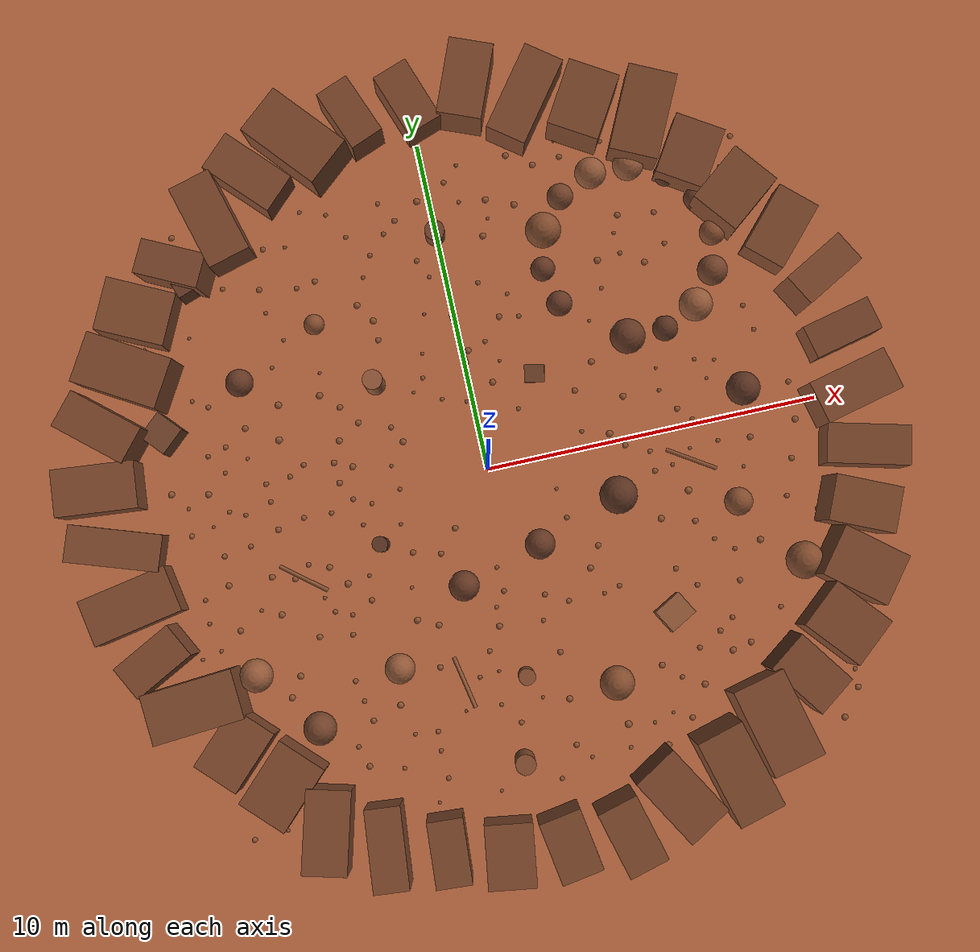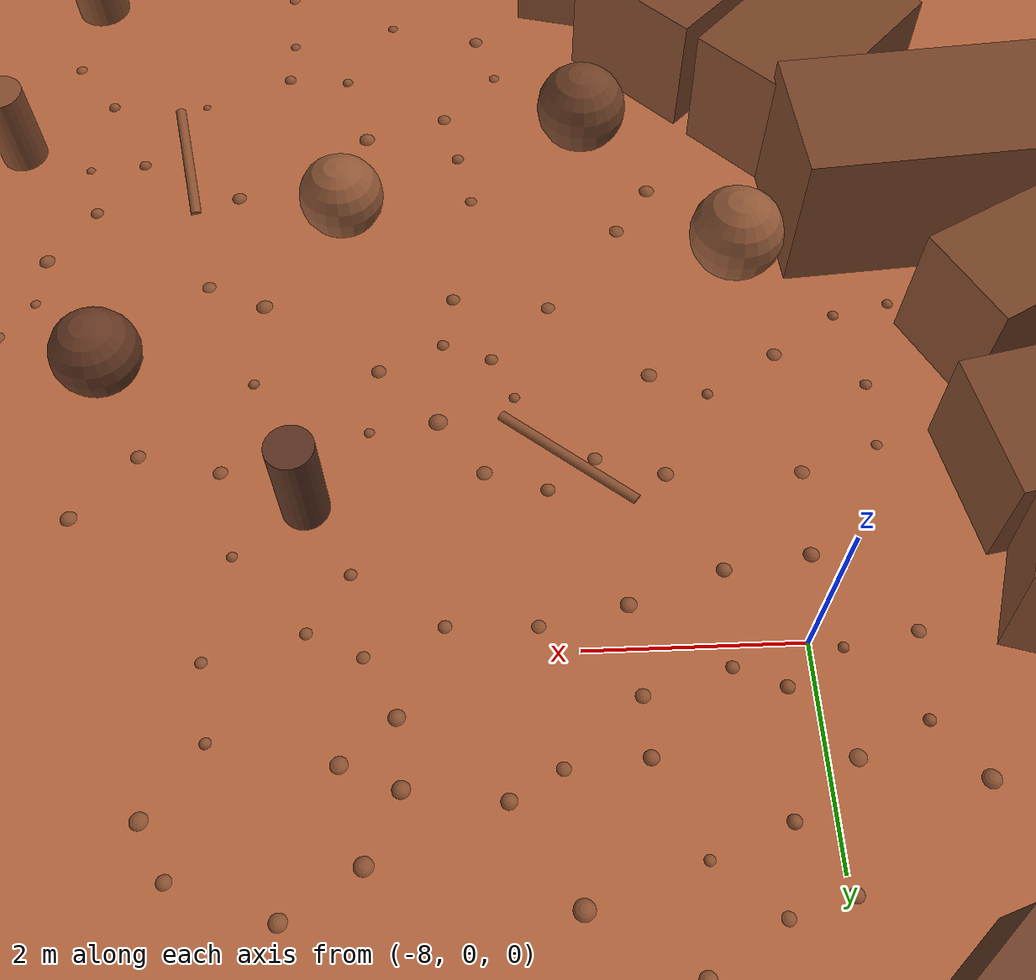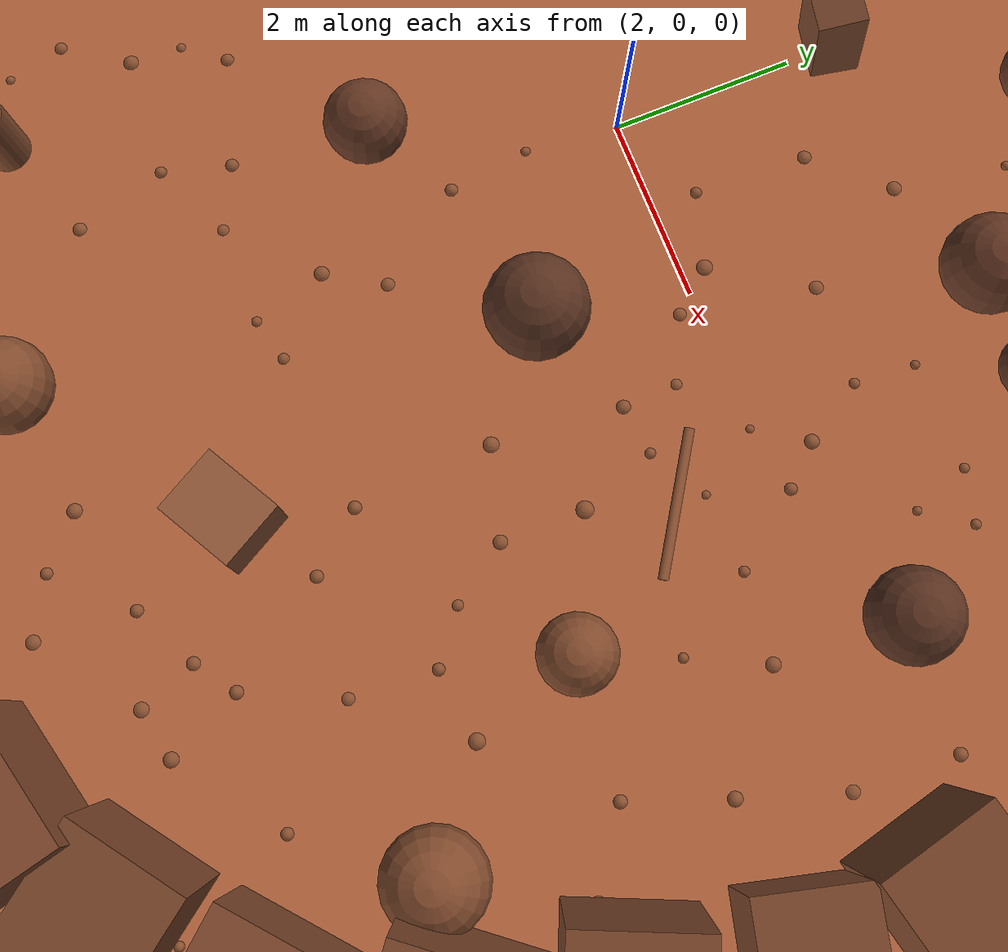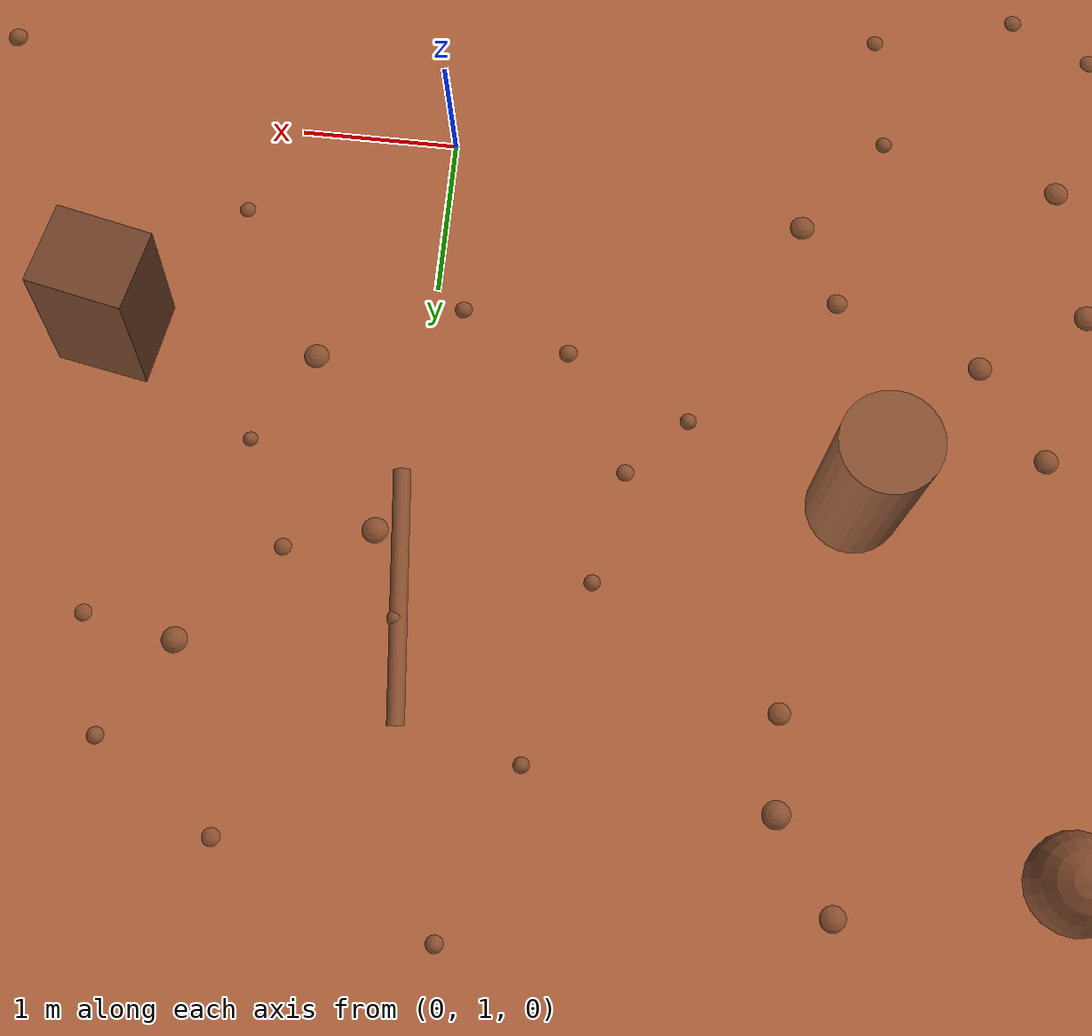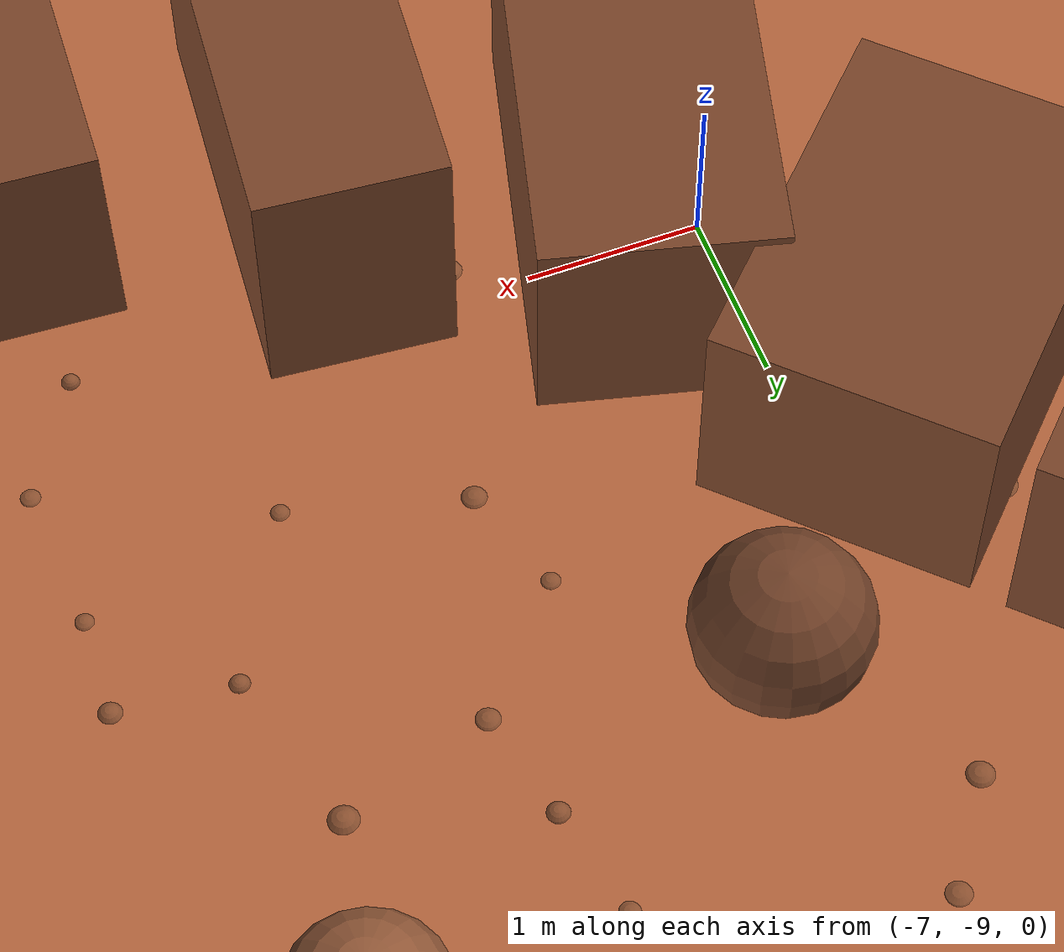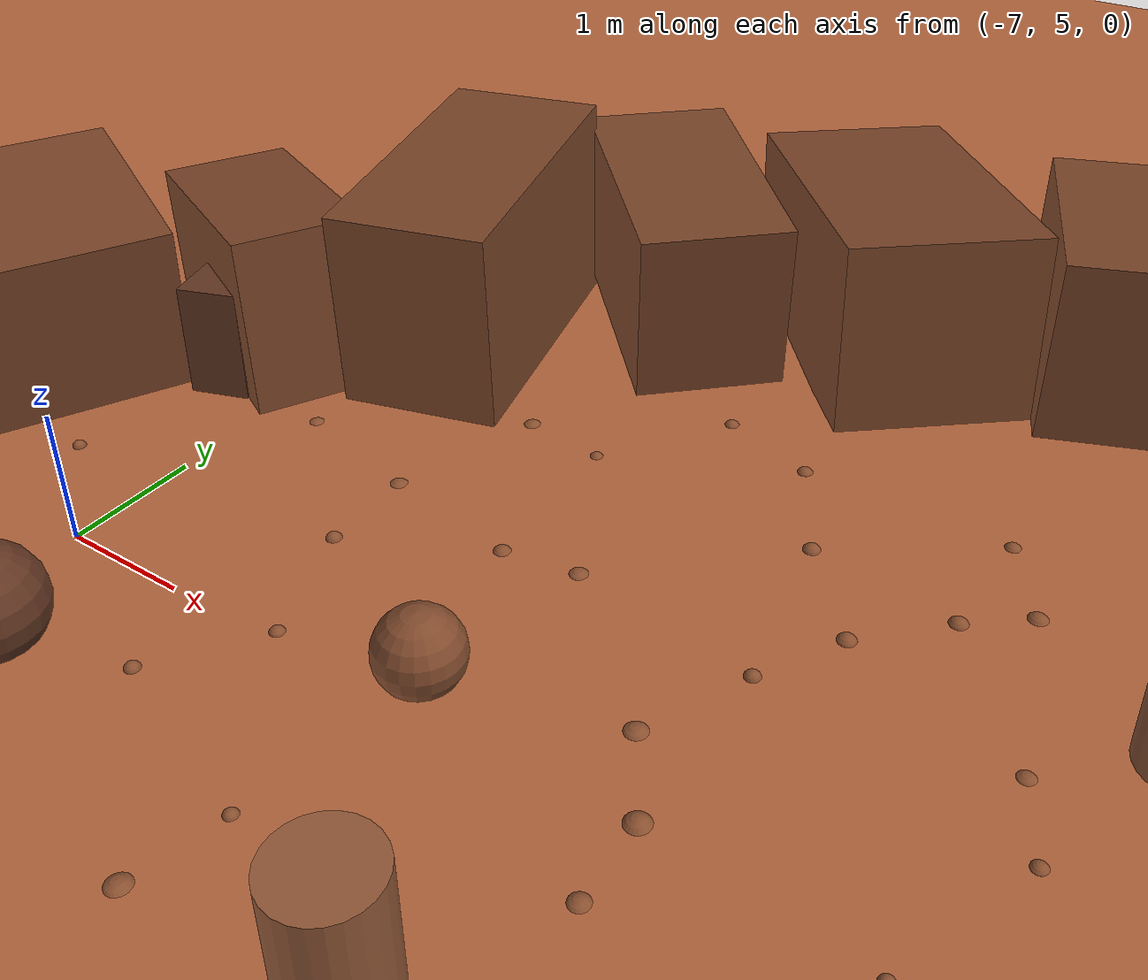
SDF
<?xml version="1.0"?>
<!-- Generated by gen_demo_world.py (seed 21) - edit the generator, not this file -->
<sdf version="1.8">
  <world name="rover_world">
    <physics name="1ms" type="ignored">
      <max_step_size>0.001</max_step_size>
      <real_time_factor>1.0</real_time_factor>
    </physics>
    <plugin filename="gz-sim-physics-system" name="gz::sim::systems::Physics"/>
    <plugin filename="gz-sim-user-commands-system" name="gz::sim::systems::UserCommands"/>
    <plugin filename="gz-sim-scene-broadcaster-system" name="gz::sim::systems::SceneBroadcaster"/>
    <plugin filename="gz-sim-sensors-system" name="gz::sim::systems::Sensors">
      <render_engine>ogre2</render_engine>
    </plugin>

    <scene>
      <ambient>0.5 0.38 0.3 1</ambient>
      <background>0.85 0.6 0.42 1</background>
    </scene>

    <light type="directional" name="sun">
      <cast_shadows>true</cast_shadows>
      <pose>0 0 10 0 0 0</pose>
      <diffuse>1.0 0.82 0.65 1</diffuse>
      <specular>0.3 0.25 0.2 1</specular>
      <direction>-0.4 0.2 -0.85</direction>
    </light>

    <model name="ground_plane">
      <static>true</static>
      <link name="link">
        <collision name="collision">
          <geometry><plane><normal>0 0 1</normal><size>60 60</size></plane></geometry>
        </collision>
        <visual name="visual">
          <geometry><plane><normal>0 0 1</normal><size>60 60</size></plane></geometry>
          <material><ambient>0.71 0.40 0.24 1</ambient><diffuse>0.71 0.40 0.24 1</diffuse></material>
        </visual>
      </link>
    </model>

    <model name="rim_0">
      <static>true</static>
      <pose>10.899 0.000 0.707 0.000 0.049 0.234</pose>
      <link name="link">
        <collision name="collision"><geometry><box><size>2.435 1.287 1.373</size></box></geometry></collision>
        <visual name="visual">
          <geometry><box><size>2.435 1.287 1.373</size></box></geometry>
          <material><ambient>0.48 0.27 0.16 1</ambient><diffuse>0.48 0.27 0.16 1</diffuse></material>
        </visual>
      </link>
    </model>
    <model name="rim_1">
      <static>true</static>
      <pose>10.971 1.738 0.652 0.000 -0.069 0.225</pose>
      <link name="link">
        <collision name="collision"><geometry><box><size>2.036 1.002 1.497</size></box></geometry></collision>
        <visual name="visual">
          <geometry><box><size>2.036 1.002 1.497</size></box></geometry>
          <material><ambient>0.48 0.27 0.16 1</ambient><diffuse>0.48 0.27 0.16 1</diffuse></material>
        </visual>
      </link>
    </model>
    <model name="rim_2">
      <static>true</static>
      <pose>10.724 3.485 0.570 0.000 0.060 0.505</pose>
      <link name="link">
        <collision name="collision"><geometry><box><size>2.033 1.025 1.998</size></box></geometry></collision>
        <visual name="visual">
          <geometry><box><size>2.033 1.025 1.998</size></box></geometry>
          <material><ambient>0.48 0.27 0.16 1</ambient><diffuse>0.48 0.27 0.16 1</diffuse></material>
        </visual>
      </link>
    </model>
    <model name="rim_3">
      <static>true</static>
      <pose>9.952 5.071 0.510 0.000 -0.021 0.833</pose>
      <link name="link">
        <collision name="collision"><geometry><box><size>2.129 1.299 1.293</size></box></geometry></collision>
        <visual name="visual">
          <geometry><box><size>2.129 1.299 1.293</size></box></geometry>
          <material><ambient>0.48 0.27 0.16 1</ambient><diffuse>0.48 0.27 0.16 1</diffuse></material>
        </visual>
      </link>
    </model>
    <model name="rim_4">
      <static>true</static>
      <pose>8.813 6.403 0.745 0.000 -0.025 0.670</pose>
      <link name="link">
        <collision name="collision"><geometry><box><size>1.925 1.557 1.563</size></box></geometry></collision>
        <visual name="visual">
          <geometry><box><size>1.925 1.557 1.563</size></box></geometry>
          <material><ambient>0.48 0.27 0.16 1</ambient><diffuse>0.48 0.27 0.16 1</diffuse></material>
        </visual>
      </link>
    </model>
    <model name="rim_5">
      <static>true</static>
      <pose>7.842 7.842 0.556 0.000 -0.047 1.010</pose>
      <link name="link">
        <collision name="collision"><geometry><box><size>1.837 1.520 1.388</size></box></geometry></collision>
        <visual name="visual">
          <geometry><box><size>1.837 1.520 1.388</size></box></geometry>
          <material><ambient>0.48 0.27 0.16 1</ambient><diffuse>0.48 0.27 0.16 1</diffuse></material>
        </visual>
      </link>
    </model>
    <model name="rim_6">
      <static>true</static>
      <pose>6.690 9.208 0.768 0.000 -0.060 1.126</pose>
      <link name="link">
        <collision name="collision"><geometry><box><size>2.555 1.458 1.665</size></box></geometry></collision>
        <visual name="visual">
          <geometry><box><size>2.555 1.458 1.665</size></box></geometry>
          <material><ambient>0.48 0.27 0.16 1</ambient><diffuse>0.48 0.27 0.16 1</diffuse></material>
        </visual>
      </link>
    </model>
    <model name="rim_7">
      <static>true</static>
      <pose>5.033 9.878 0.748 0.000 -0.022 1.027</pose>
      <link name="link">
        <collision name="collision"><geometry><box><size>2.001 1.554 1.910</size></box></geometry></collision>
        <visual name="visual">
          <geometry><box><size>2.001 1.554 1.910</size></box></geometry>
          <material><ambient>0.48 0.27 0.16 1</ambient><diffuse>0.48 0.27 0.16 1</diffuse></material>
        </visual>
      </link>
    </model>
    <model name="rim_8">
      <static>true</static>
      <pose>3.421 10.529 0.616 0.000 0.035 0.931</pose>
      <link name="link">
        <collision name="collision"><geometry><box><size>2.795 1.232 1.221</size></box></geometry></collision>
        <visual name="visual">
          <geometry><box><size>2.795 1.232 1.221</size></box></geometry>
          <material><ambient>0.48 0.27 0.16 1</ambient><diffuse>0.48 0.27 0.16 1</diffuse></material>
        </visual>
      </link>
    </model>
    <model name="rim_9">
      <static>true</static>
      <pose>1.783 11.255 0.649 0.000 0.017 1.191</pose>
      <link name="link">
        <collision name="collision"><geometry><box><size>2.292 1.330 1.799</size></box></geometry></collision>
        <visual name="visual">
          <geometry><box><size>2.292 1.330 1.799</size></box></geometry>
          <material><ambient>0.48 0.27 0.16 1</ambient><diffuse>0.48 0.27 0.16 1</diffuse></material>
        </visual>
      </link>
    </model>
    <model name="rim_10">
      <static>true</static>
      <pose>0.000 11.134 0.687 0.000 -0.025 1.912</pose>
      <link name="link">
        <collision name="collision"><geometry><box><size>1.981 1.102 1.479</size></box></geometry></collision>
        <visual name="visual">
          <geometry><box><size>1.981 1.102 1.479</size></box></geometry>
          <material><ambient>0.48 0.27 0.16 1</ambient><diffuse>0.48 0.27 0.16 1</diffuse></material>
        </visual>
      </link>
    </model>
    <model name="rim_11">
      <static>true</static>
      <pose>-1.746 11.021 0.592 0.000 -0.020 1.949</pose>
      <link name="link">
        <collision name="collision"><geometry><box><size>1.903 1.039 1.851</size></box></geometry></collision>
        <visual name="visual">
          <geometry><box><size>1.903 1.039 1.851</size></box></geometry>
          <material><ambient>0.48 0.27 0.16 1</ambient><diffuse>0.48 0.27 0.16 1</diffuse></material>
        </visual>
      </link>
    </model>
    <model name="rim_12">
      <static>true</static>
      <pose>-3.464 10.661 0.703 0.000 0.074 2.276</pose>
      <link name="link">
        <collision name="collision"><geometry><box><size>2.699 1.575 1.526</size></box></geometry></collision>
        <visual name="visual">
          <geometry><box><size>2.699 1.575 1.526</size></box></geometry>
          <material><ambient>0.48 0.27 0.16 1</ambient><diffuse>0.48 0.27 0.16 1</diffuse></material>
        </visual>
      </link>
    </model>
    <model name="rim_13">
      <static>true</static>
      <pose>-5.064 9.939 0.765 0.000 -0.054 2.343</pose>
      <link name="link">
        <collision name="collision"><geometry><box><size>2.291 1.225 1.398</size></box></geometry></collision>
        <visual name="visual">
          <geometry><box><size>2.291 1.225 1.398</size></box></geometry>
          <material><ambient>0.48 0.27 0.16 1</ambient><diffuse>0.48 0.27 0.16 1</diffuse></material>
        </visual>
      </link>
    </model>
    <model name="rim_14">
      <static>true</static>
      <pose>-6.373 8.771 0.742 0.000 -0.039 1.841</pose>
      <link name="link">
        <collision name="collision"><geometry><box><size>2.574 1.290 1.870</size></box></geometry></collision>
        <visual name="visual">
          <geometry><box><size>2.574 1.290 1.870</size></box></geometry>
          <material><ambient>0.48 0.27 0.16 1</ambient><diffuse>0.48 0.27 0.16 1</diffuse></material>
        </visual>
      </link>
    </model>
    <model name="rim_15">
      <static>true</static>
      <pose>-7.760 7.760 0.626 0.000 0.077 2.676</pose>
      <link name="link">
        <collision name="collision"><geometry><box><size>1.971 1.042 1.470</size></box></geometry></collision>
        <visual name="visual">
          <geometry><box><size>1.971 1.042 1.470</size></box></geometry>
          <material><ambient>0.48 0.27 0.16 1</ambient><diffuse>0.48 0.27 0.16 1</diffuse></material>
        </visual>
      </link>
    </model>
    <model name="rim_16">
      <static>true</static>
      <pose>-9.099 6.611 0.644 0.000 -0.075 2.696</pose>
      <link name="link">
        <collision name="collision"><geometry><box><size>2.052 1.575 1.621</size></box></geometry></collision>
        <visual name="visual">
          <geometry><box><size>2.052 1.575 1.621</size></box></geometry>
          <material><ambient>0.48 0.27 0.16 1</ambient><diffuse>0.48 0.27 0.16 1</diffuse></material>
        </visual>
      </link>
    </model>
    <model name="rim_17">
      <static>true</static>
      <pose>-9.736 4.961 0.751 0.000 0.013 2.611</pose>
      <link name="link">
        <collision name="collision"><geometry><box><size>2.595 1.529 1.681</size></box></geometry></collision>
        <visual name="visual">
          <geometry><box><size>2.595 1.529 1.681</size></box></geometry>
          <material><ambient>0.48 0.27 0.16 1</ambient><diffuse>0.48 0.27 0.16 1</diffuse></material>
        </visual>
      </link>
    </model>
    <model name="rim_18">
      <static>true</static>
      <pose>-10.756 3.495 0.592 0.000 0.030 2.436</pose>
      <link name="link">
        <collision name="collision"><geometry><box><size>2.334 1.166 1.815</size></box></geometry></collision>
        <visual name="visual">
          <geometry><box><size>2.334 1.166 1.815</size></box></geometry>
          <material><ambient>0.48 0.27 0.16 1</ambient><diffuse>0.48 0.27 0.16 1</diffuse></material>
        </visual>
      </link>
    </model>
    <model name="rim_19">
      <static>true</static>
      <pose>-11.232 1.779 0.507 0.000 -0.039 3.052</pose>
      <link name="link">
        <collision name="collision"><geometry><box><size>2.394 1.386 1.881</size></box></geometry></collision>
        <visual name="visual">
          <geometry><box><size>2.394 1.386 1.881</size></box></geometry>
          <material><ambient>0.48 0.27 0.16 1</ambient><diffuse>0.48 0.27 0.16 1</diffuse></material>
        </visual>
      </link>
    </model>
    <model name="rim_20">
      <static>true</static>
      <pose>-11.043 0.000 0.788 0.000 -0.076 2.817</pose>
      <link name="link">
        <collision name="collision"><geometry><box><size>2.706 1.080 1.276</size></box></geometry></collision>
        <visual name="visual">
          <geometry><box><size>2.706 1.080 1.276</size></box></geometry>
          <material><ambient>0.48 0.27 0.16 1</ambient><diffuse>0.48 0.27 0.16 1</diffuse></material>
        </visual>
      </link>
    </model>
    <model name="rim_21">
      <static>true</static>
      <pose>-10.932 -1.731 0.542 0.000 -0.028 3.330</pose>
      <link name="link">
        <collision name="collision"><geometry><box><size>2.667 1.393 1.301</size></box></geometry></collision>
        <visual name="visual">
          <geometry><box><size>2.667 1.393 1.301</size></box></geometry>
          <material><ambient>0.48 0.27 0.16 1</ambient><diffuse>0.48 0.27 0.16 1</diffuse></material>
        </visual>
      </link>
    </model>
    <model name="rim_22">
      <static>true</static>
      <pose>-10.553 -3.429 0.566 0.000 0.008 3.624</pose>
      <link name="link">
        <collision name="collision"><geometry><box><size>1.966 1.110 1.502</size></box></geometry></collision>
        <visual name="visual">
          <geometry><box><size>1.966 1.110 1.502</size></box></geometry>
          <material><ambient>0.48 0.27 0.16 1</ambient><diffuse>0.48 0.27 0.16 1</diffuse></material>
        </visual>
      </link>
    </model>
    <model name="rim_23">
      <static>true</static>
      <pose>-9.648 -4.916 0.713 0.000 -0.006 3.219</pose>
      <link name="link">
        <collision name="collision"><geometry><box><size>2.674 1.465 1.833</size></box></geometry></collision>
        <visual name="visual">
          <geometry><box><size>2.674 1.465 1.833</size></box></geometry>
          <material><ambient>0.48 0.27 0.16 1</ambient><diffuse>0.48 0.27 0.16 1</diffuse></material>
        </visual>
      </link>
    </model>
    <model name="rim_24">
      <static>true</static>
      <pose>-8.768 -6.370 0.729 0.000 -0.030 3.927</pose>
      <link name="link">
        <collision name="collision"><geometry><box><size>1.975 1.427 1.402</size></box></geometry></collision>
        <visual name="visual">
          <geometry><box><size>1.975 1.427 1.402</size></box></geometry>
          <material><ambient>0.48 0.27 0.16 1</ambient><diffuse>0.48 0.27 0.16 1</diffuse></material>
        </visual>
      </link>
    </model>
    <model name="rim_25">
      <static>true</static>
      <pose>-7.655 -7.655 0.617 0.000 0.008 3.929</pose>
      <link name="link">
        <collision name="collision"><geometry><box><size>2.109 1.540 1.436</size></box></geometry></collision>
        <visual name="visual">
          <geometry><box><size>2.109 1.540 1.436</size></box></geometry>
          <material><ambient>0.48 0.27 0.16 1</ambient><diffuse>0.48 0.27 0.16 1</diffuse></material>
        </visual>
      </link>
    </model>
    <model name="rim_26">
      <static>true</static>
      <pose>-6.682 -9.198 0.530 0.000 -0.030 4.458</pose>
      <link name="link">
        <collision name="collision"><geometry><box><size>2.401 1.305 1.788</size></box></geometry></collision>
        <visual name="visual">
          <geometry><box><size>2.401 1.305 1.788</size></box></geometry>
          <material><ambient>0.48 0.27 0.16 1</ambient><diffuse>0.48 0.27 0.16 1</diffuse></material>
        </visual>
      </link>
    </model>
    <model name="rim_27">
      <static>true</static>
      <pose>-5.094 -9.997 0.658 0.000 -0.023 4.623</pose>
      <link name="link">
        <collision name="collision"><geometry><box><size>2.361 1.038 1.852</size></box></geometry></collision>
        <visual name="visual">
          <geometry><box><size>2.361 1.038 1.852</size></box></geometry>
          <material><ambient>0.48 0.27 0.16 1</ambient><diffuse>0.48 0.27 0.16 1</diffuse></material>
        </visual>
      </link>
    </model>
    <model name="rim_28">
      <static>true</static>
      <pose>-3.396 -10.453 0.798 0.000 0.042 4.650</pose>
      <link name="link">
        <collision name="collision"><geometry><box><size>1.908 1.046 1.259</size></box></geometry></collision>
        <visual name="visual">
          <geometry><box><size>1.908 1.046 1.259</size></box></geometry>
          <material><ambient>0.48 0.27 0.16 1</ambient><diffuse>0.48 0.27 0.16 1</diffuse></material>
        </visual>
      </link>
    </model>
    <model name="rim_29">
      <static>true</static>
      <pose>-1.732 -10.933 0.686 0.000 -0.018 4.569</pose>
      <link name="link">
        <collision name="collision"><geometry><box><size>1.820 1.387 1.554</size></box></geometry></collision>
        <visual name="visual">
          <geometry><box><size>1.820 1.387 1.554</size></box></geometry>
          <material><ambient>0.48 0.27 0.16 1</ambient><diffuse>0.48 0.27 0.16 1</diffuse></material>
        </visual>
      </link>
    </model>
    <model name="rim_30">
      <static>true</static>
      <pose>-0.000 -11.041 0.568 0.000 0.051 4.876</pose>
      <link name="link">
        <collision name="collision"><geometry><box><size>1.849 1.260 1.398</size></box></geometry></collision>
        <visual name="visual">
          <geometry><box><size>1.849 1.260 1.398</size></box></geometry>
          <material><ambient>0.48 0.27 0.16 1</ambient><diffuse>0.48 0.27 0.16 1</diffuse></material>
        </visual>
      </link>
    </model>
    <model name="rim_31">
      <static>true</static>
      <pose>1.757 -11.096 0.637 0.000 0.074 4.975</pose>
      <link name="link">
        <collision name="collision"><geometry><box><size>2.036 1.231 1.589</size></box></geometry></collision>
        <visual name="visual">
          <geometry><box><size>2.036 1.231 1.589</size></box></geometry>
          <material><ambient>0.48 0.27 0.16 1</ambient><diffuse>0.48 0.27 0.16 1</diffuse></material>
        </visual>
      </link>
    </model>
    <model name="rim_32">
      <static>true</static>
      <pose>3.353 -10.320 0.644 0.000 0.020 5.250</pose>
      <link name="link">
        <collision name="collision"><geometry><box><size>2.292 1.430 1.912</size></box></geometry></collision>
        <visual name="visual">
          <geometry><box><size>2.292 1.430 1.912</size></box></geometry>
          <material><ambient>0.48 0.27 0.16 1</ambient><diffuse>0.48 0.27 0.16 1</diffuse></material>
        </visual>
      </link>
    </model>
    <model name="rim_33">
      <static>true</static>
      <pose>5.110 -10.028 0.700 0.000 0.067 4.980</pose>
      <link name="link">
        <collision name="collision"><geometry><box><size>2.659 1.419 1.746</size></box></geometry></collision>
        <visual name="visual">
          <geometry><box><size>2.659 1.419 1.746</size></box></geometry>
          <material><ambient>0.48 0.27 0.16 1</ambient><diffuse>0.48 0.27 0.16 1</diffuse></material>
        </visual>
      </link>
    </model>
    <model name="rim_34">
      <static>true</static>
      <pose>6.484 -8.925 0.684 0.000 -0.030 4.946</pose>
      <link name="link">
        <collision name="collision"><geometry><box><size>2.625 1.578 1.991</size></box></geometry></collision>
        <visual name="visual">
          <geometry><box><size>2.625 1.578 1.991</size></box></geometry>
          <material><ambient>0.48 0.27 0.16 1</ambient><diffuse>0.48 0.27 0.16 1</diffuse></material>
        </visual>
      </link>
    </model>
    <model name="rim_35">
      <static>true</static>
      <pose>7.769 -7.769 0.617 0.000 0.071 5.340</pose>
      <link name="link">
        <collision name="collision"><geometry><box><size>1.945 1.332 1.264</size></box></geometry></collision>
        <visual name="visual">
          <geometry><box><size>1.945 1.332 1.264</size></box></geometry>
          <material><ambient>0.48 0.27 0.16 1</ambient><diffuse>0.48 0.27 0.16 1</diffuse></material>
        </visual>
      </link>
    </model>
    <model name="rim_36">
      <static>true</static>
      <pose>9.098 -6.610 0.639 0.000 -0.026 5.420</pose>
      <link name="link">
        <collision name="collision"><geometry><box><size>1.908 1.574 1.763</size></box></geometry></collision>
        <visual name="visual">
          <geometry><box><size>1.908 1.574 1.763</size></box></geometry>
          <material><ambient>0.48 0.27 0.16 1</ambient><diffuse>0.48 0.27 0.16 1</diffuse></material>
        </visual>
      </link>
    </model>
    <model name="rim_37">
      <static>true</static>
      <pose>9.966 -5.078 0.704 0.000 0.055 5.615</pose>
      <link name="link">
        <collision name="collision"><geometry><box><size>2.061 1.571 1.458</size></box></geometry></collision>
        <visual name="visual">
          <geometry><box><size>2.061 1.571 1.458</size></box></geometry>
          <material><ambient>0.48 0.27 0.16 1</ambient><diffuse>0.48 0.27 0.16 1</diffuse></material>
        </visual>
      </link>
    </model>
    <model name="rim_38">
      <static>true</static>
      <pose>10.359 -3.366 0.704 0.000 0.071 5.872</pose>
      <link name="link">
        <collision name="collision"><geometry><box><size>2.000 1.359 1.422</size></box></geometry></collision>
        <visual name="visual">
          <geometry><box><size>2.000 1.359 1.422</size></box></geometry>
          <material><ambient>0.48 0.27 0.16 1</ambient><diffuse>0.48 0.27 0.16 1</diffuse></material>
        </visual>
      </link>
    </model>
    <model name="rim_39">
      <static>true</static>
      <pose>10.944 -1.733 0.631 0.000 -0.036 6.034</pose>
      <link name="link">
        <collision name="collision"><geometry><box><size>2.417 1.168 1.339</size></box></geometry></collision>
        <visual name="visual">
          <geometry><box><size>2.417 1.168 1.339</size></box></geometry>
          <material><ambient>0.48 0.27 0.16 1</ambient><diffuse>0.48 0.27 0.16 1</diffuse></material>
        </visual>
      </link>
    </model>
    <model name="crater_0">
      <static>true</static>
      <pose>8.100 5.500 0.213 0 0 0</pose>
      <link name="link">
        <collision name="collision"><geometry><sphere><radius>0.388</radius></sphere></geometry></collision>
        <visual name="visual">
          <geometry><sphere><radius>0.388</radius></sphere></geometry>
          <material><ambient>0.52 0.30 0.18 1</ambient><diffuse>0.52 0.30 0.18 1</diffuse></material>
        </visual>
      </link>
    </model>
    <model name="crater_1">
      <static>true</static>
      <pose>7.843 6.628 0.196 0 0 0</pose>
      <link name="link">
        <collision name="collision"><geometry><sphere><radius>0.357</radius></sphere></geometry></collision>
        <visual name="visual">
          <geometry><sphere><radius>0.357</radius></sphere></geometry>
          <material><ambient>0.40 0.22 0.14 1</ambient><diffuse>0.40 0.22 0.14 1</diffuse></material>
        </visual>
      </link>
    </model>
    <model name="crater_2">
      <static>true</static>
      <pose>7.121 7.533 0.195 0 0 0</pose>
      <link name="link">
        <collision name="collision"><geometry><sphere><radius>0.354</radius></sphere></geometry></collision>
        <visual name="visual">
          <geometry><sphere><radius>0.354</radius></sphere></geometry>
          <material><ambient>0.36 0.20 0.13 1</ambient><diffuse>0.36 0.20 0.13 1</diffuse></material>
        </visual>
      </link>
    </model>
    <model name="crater_3">
      <static>true</static>
      <pose>6.079 8.035 0.256 0 0 0</pose>
      <link name="link">
        <collision name="collision"><geometry><sphere><radius>0.466</radius></sphere></geometry></collision>
        <visual name="visual">
          <geometry><sphere><radius>0.466</radius></sphere></geometry>
          <material><ambient>0.58 0.35 0.22 1</ambient><diffuse>0.58 0.35 0.22 1</diffuse></material>
        </visual>
      </link>
    </model>
    <model name="crater_4">
      <static>true</static>
      <pose>4.921 8.035 0.259 0 0 0</pose>
      <link name="link">
        <collision name="collision"><geometry><sphere><radius>0.472</radius></sphere></geometry></collision>
        <visual name="visual">
          <geometry><sphere><radius>0.472</radius></sphere></geometry>
          <material><ambient>0.58 0.35 0.22 1</ambient><diffuse>0.58 0.35 0.22 1</diffuse></material>
        </visual>
      </link>
    </model>
    <model name="crater_5">
      <static>true</static>
      <pose>3.879 7.533 0.219 0 0 0</pose>
      <link name="link">
        <collision name="collision"><geometry><sphere><radius>0.398</radius></sphere></geometry></collision>
        <visual name="visual">
          <geometry><sphere><radius>0.398</radius></sphere></geometry>
          <material><ambient>0.45 0.26 0.16 1</ambient><diffuse>0.45 0.26 0.16 1</diffuse></material>
        </visual>
      </link>
    </model>
    <model name="crater_6">
      <static>true</static>
      <pose>3.157 6.628 0.296 0 0 0</pose>
      <link name="link">
        <collision name="collision"><geometry><sphere><radius>0.538</radius></sphere></geometry></collision>
        <visual name="visual">
          <geometry><sphere><radius>0.538</radius></sphere></geometry>
          <material><ambient>0.52 0.30 0.18 1</ambient><diffuse>0.52 0.30 0.18 1</diffuse></material>
        </visual>
      </link>
    </model>
    <model name="crater_7">
      <static>true</static>
      <pose>2.900 5.500 0.203 0 0 0</pose>
      <link name="link">
        <collision name="collision"><geometry><sphere><radius>0.369</radius></sphere></geometry></collision>
        <visual name="visual">
          <geometry><sphere><radius>0.369</radius></sphere></geometry>
          <material><ambient>0.40 0.22 0.14 1</ambient><diffuse>0.40 0.22 0.14 1</diffuse></material>
        </visual>
      </link>
    </model>
    <model name="crater_8">
      <static>true</static>
      <pose>3.157 4.372 0.213 0 0 0</pose>
      <link name="link">
        <collision name="collision"><geometry><sphere><radius>0.388</radius></sphere></geometry></collision>
        <visual name="visual">
          <geometry><sphere><radius>0.388</radius></sphere></geometry>
          <material><ambient>0.40 0.22 0.14 1</ambient><diffuse>0.40 0.22 0.14 1</diffuse></material>
        </visual>
      </link>
    </model>
    <model name="crater_10">
      <static>true</static>
      <pose>4.921 2.965 0.291 0 0 0</pose>
      <link name="link">
        <collision name="collision"><geometry><sphere><radius>0.529</radius></sphere></geometry></collision>
        <visual name="visual">
          <geometry><sphere><radius>0.529</radius></sphere></geometry>
          <material><ambient>0.40 0.22 0.14 1</ambient><diffuse>0.40 0.22 0.14 1</diffuse></material>
        </visual>
      </link>
    </model>
    <model name="crater_11">
      <static>true</static>
      <pose>6.079 2.965 0.211 0 0 0</pose>
      <link name="link">
        <collision name="collision"><geometry><sphere><radius>0.383</radius></sphere></geometry></collision>
        <visual name="visual">
          <geometry><sphere><radius>0.383</radius></sphere></geometry>
          <material><ambient>0.36 0.20 0.13 1</ambient><diffuse>0.36 0.20 0.13 1</diffuse></material>
        </visual>
      </link>
    </model>
    <model name="crater_12">
      <static>true</static>
      <pose>7.121 3.467 0.280 0 0 0</pose>
      <link name="link">
        <collision name="collision"><geometry><sphere><radius>0.508</radius></sphere></geometry></collision>
        <visual name="visual">
          <geometry><sphere><radius>0.508</radius></sphere></geometry>
          <material><ambient>0.58 0.35 0.22 1</ambient><diffuse>0.58 0.35 0.22 1</diffuse></material>
        </visual>
      </link>
    </model>
    <model name="crater_13">
      <static>true</static>
      <pose>7.843 4.372 0.251 0 0 0</pose>
      <link name="link">
        <collision name="collision"><geometry><sphere><radius>0.456</radius></sphere></geometry></collision>
        <visual name="visual">
          <geometry><sphere><radius>0.456</radius></sphere></geometry>
          <material><ambient>0.45 0.26 0.16 1</ambient><diffuse>0.45 0.26 0.16 1</diffuse></material>
        </visual>
      </link>
    </model>
    <model name="rock_c0">
      <static>true</static>
      <pose>-3.521 -1.525 0.551 0 0 0</pose>
      <link name="link">
        <collision name="collision"><geometry><cylinder><radius>0.229</radius><length>1.102</length></cylinder></geometry></collision>
        <visual name="visual">
          <geometry><cylinder><radius>0.229</radius><length>1.102</length></cylinder></geometry>
          <material><ambient>0.36 0.20 0.13 1</ambient><diffuse>0.36 0.20 0.13 1</diffuse></material>
        </visual>
      </link>
    </model>
    <model name="rock_b1">
      <static>true</static>
      <pose>-7.720 7.354 0.312 -0.007 0.029 1.904</pose>
      <link name="link">
        <collision name="collision"><geometry><box><size>1.031 0.494 1.171</size></box></geometry></collision>
        <visual name="visual">
          <geometry><box><size>1.031 0.494 1.171</size></box></geometry>
          <material><ambient>0.40 0.22 0.14 1</ambient><diffuse>0.40 0.22 0.14 1</diffuse></material>
        </visual>
      </link>
    </model>
    <model name="rock_s2">
      <static>true</static>
      <pose>-6.390 -6.376 0.271 0 0 0</pose>
      <link name="link">
        <collision name="collision"><geometry><sphere><radius>0.492</radius></sphere></geometry></collision>
        <visual name="visual">
          <geometry><sphere><radius>0.492</radius></sphere></geometry>
          <material><ambient>0.45 0.26 0.16 1</ambient><diffuse>0.45 0.26 0.16 1</diffuse></material>
        </visual>
      </link>
    </model>
    <model name="rock_s3">
      <static>true</static>
      <pose>7.179 -7.893 0.249 0 0 0</pose>
      <link name="link">
        <collision name="collision"><geometry><sphere><radius>0.454</radius></sphere></geometry></collision>
        <visual name="visual">
          <geometry><sphere><radius>0.454</radius></sphere></geometry>
          <material><ambient>0.52 0.30 0.18 1</ambient><diffuse>0.52 0.30 0.18 1</diffuse></material>
        </visual>
      </link>
    </model>
    <model name="rock_s4">
      <static>true</static>
      <pose>-4.135 5.323 0.170 0 0 0</pose>
      <link name="link">
        <collision name="collision"><geometry><sphere><radius>0.310</radius></sphere></geometry></collision>
        <visual name="visual">
          <geometry><sphere><radius>0.310</radius></sphere></geometry>
          <material><ambient>0.52 0.30 0.18 1</ambient><diffuse>0.52 0.30 0.18 1</diffuse></material>
        </visual>
      </link>
    </model>
    <model name="rock_s5">
      <static>true</static>
      <pose>7.928 0.709 0.279 0 0 0</pose>
      <link name="link">
        <collision name="collision"><geometry><sphere><radius>0.507</radius></sphere></geometry></collision>
        <visual name="visual">
          <geometry><sphere><radius>0.507</radius></sphere></geometry>
          <material><ambient>0.36 0.20 0.13 1</ambient><diffuse>0.36 0.20 0.13 1</diffuse></material>
        </visual>
      </link>
    </model>
    <model name="rock_s6">
      <static>true</static>
      <pose>-1.408 -3.227 0.248 0 0 0</pose>
      <link name="link">
        <collision name="collision"><geometry><sphere><radius>0.451</radius></sphere></geometry></collision>
        <visual name="visual">
          <geometry><sphere><radius>0.451</radius></sphere></geometry>
          <material><ambient>0.40 0.22 0.14 1</ambient><diffuse>0.40 0.22 0.14 1</diffuse></material>
        </visual>
      </link>
    </model>
    <model name="rock_b7">
      <static>true</static>
      <pose>1.963 2.447 0.396 -0.053 -0.115 1.386</pose>
      <link name="link">
        <collision name="collision"><geometry><box><size>0.515 0.584 1.205</size></box></geometry></collision>
        <visual name="visual">
          <geometry><box><size>0.515 0.584 1.205</size></box></geometry>
          <material><ambient>0.45 0.26 0.16 1</ambient><diffuse>0.45 0.26 0.16 1</diffuse></material>
        </visual>
      </link>
    </model>
    <model name="rock_s8">
      <static>true</static>
      <pose>7.043 -2.533 0.232 0 0 0</pose>
      <link name="link">
        <collision name="collision"><geometry><sphere><radius>0.422</radius></sphere></geometry></collision>
        <visual name="visual">
          <geometry><sphere><radius>0.422</radius></sphere></geometry>
          <material><ambient>0.52 0.30 0.18 1</ambient><diffuse>0.52 0.30 0.18 1</diffuse></material>
        </visual>
      </link>
    </model>
    <model name="rock_c9">
      <static>true</static>
      <pose>-2.725 3.162 0.698 0 0 0</pose>
      <link name="link">
        <collision name="collision"><geometry><cylinder><radius>0.295</radius><length>1.396</length></cylinder></geometry></collision>
        <visual name="visual">
          <geometry><cylinder><radius>0.295</radius><length>1.396</length></cylinder></geometry>
          <material><ambient>0.58 0.35 0.22 1</ambient><diffuse>0.58 0.35 0.22 1</diffuse></material>
        </visual>
      </link>
    </model>
    <model name="rock_b10">
      <static>true</static>
      <pose>4.448 -5.287 0.359 -0.009 0.027 2.079</pose>
      <link name="link">
        <collision name="collision"><geometry><box><size>0.759 0.896 0.713</size></box></geometry></collision>
        <visual name="visual">
          <geometry><box><size>0.759 0.896 0.713</size></box></geometry>
          <material><ambient>0.58 0.35 0.22 1</ambient><diffuse>0.58 0.35 0.22 1</diffuse></material>
        </visual>
      </link>
    </model>
    <model name="rock_c11">
      <static>true</static>
      <pose>-0.758 -8.546 0.631 0 0 0</pose>
      <link name="link">
        <collision name="collision"><geometry><cylinder><radius>0.297</radius><length>1.262</length></cylinder></geometry></collision>
        <visual name="visual">
          <geometry><cylinder><radius>0.297</radius><length>1.262</length></cylinder></geometry>
          <material><ambient>0.52 0.30 0.18 1</ambient><diffuse>0.52 0.30 0.18 1</diffuse></material>
        </visual>
      </link>
    </model>
    <model name="rock_b12">
      <static>true</static>
      <pose>-9.131 3.024 0.339 -0.004 0.075 2.305</pose>
      <link name="link">
        <collision name="collision"><geometry><box><size>0.904 0.899 0.759</size></box></geometry></collision>
        <visual name="visual">
          <geometry><box><size>0.904 0.899 0.759</size></box></geometry>
          <material><ambient>0.45 0.26 0.16 1</ambient><diffuse>0.45 0.26 0.16 1</diffuse></material>
        </visual>
      </link>
    </model>
    <model name="rock_s13">
      <static>true</static>
      <pose>-7.899 -4.481 0.273 0 0 0</pose>
      <link name="link">
        <collision name="collision"><geometry><sphere><radius>0.497</radius></sphere></geometry></collision>
        <visual name="visual">
          <geometry><sphere><radius>0.497</radius></sphere></geometry>
          <material><ambient>0.58 0.35 0.22 1</ambient><diffuse>0.58 0.35 0.22 1</diffuse></material>
        </visual>
      </link>
    </model>
    <model name="rock_s14">
      <static>true</static>
      <pose>-3.757 -5.185 0.247 0 0 0</pose>
      <link name="link">
        <collision name="collision"><geometry><sphere><radius>0.449</radius></sphere></geometry></collision>
        <visual name="visual">
          <geometry><sphere><radius>0.449</radius></sphere></geometry>
          <material><ambient>0.58 0.35 0.22 1</ambient><diffuse>0.58 0.35 0.22 1</diffuse></material>
        </visual>
      </link>
    </model>
    <model name="rock_s15">
      <static>true</static>
      <pose>3.613 -1.589 0.310 0 0 0</pose>
      <link name="link">
        <collision name="collision"><geometry><sphere><radius>0.564</radius></sphere></geometry></collision>
        <visual name="visual">
          <geometry><sphere><radius>0.564</radius></sphere></geometry>
          <material><ambient>0.36 0.20 0.13 1</ambient><diffuse>0.36 0.20 0.13 1</diffuse></material>
        </visual>
      </link>
    </model>
    <model name="rock_c16">
      <static>true</static>
      <pose>-0.182 -6.163 0.465 0 0 0</pose>
      <link name="link">
        <collision name="collision"><geometry><cylinder><radius>0.245</radius><length>0.930</length></cylinder></geometry></collision>
        <visual name="visual">
          <geometry><cylinder><radius>0.245</radius><length>0.930</length></cylinder></geometry>
          <material><ambient>0.52 0.30 0.18 1</ambient><diffuse>0.52 0.30 0.18 1</diffuse></material>
        </visual>
      </link>
    </model>
    <model name="rock_s17">
      <static>true</static>
      <pose>2.365 -6.950 0.281 0 0 0</pose>
      <link name="link">
        <collision name="collision"><geometry><sphere><radius>0.510</radius></sphere></geometry></collision>
        <visual name="visual">
          <geometry><sphere><radius>0.510</radius></sphere></geometry>
          <material><ambient>0.52 0.30 0.18 1</ambient><diffuse>0.52 0.30 0.18 1</diffuse></material>
        </visual>
      </link>
    </model>
    <model name="rock_c18">
      <static>true</static>
      <pose>-0.029 7.203 0.414 0 0 0</pose>
      <link name="link">
        <collision name="collision"><geometry><cylinder><radius>0.296</radius><length>0.827</length></cylinder></geometry></collision>
        <visual name="visual">
          <geometry><cylinder><radius>0.296</radius><length>0.827</length></cylinder></geometry>
          <material><ambient>0.45 0.26 0.16 1</ambient><diffuse>0.45 0.26 0.16 1</diffuse></material>
        </visual>
      </link>
    </model>
    <model name="rock_s19">
      <static>true</static>
      <pose>-6.661 4.070 0.229 0 0 0</pose>
      <link name="link">
        <collision name="collision"><geometry><sphere><radius>0.417</radius></sphere></geometry></collision>
        <visual name="visual">
          <geometry><sphere><radius>0.417</radius></sphere></geometry>
          <material><ambient>0.40 0.22 0.14 1</ambient><diffuse>0.40 0.22 0.14 1</diffuse></material>
        </visual>
      </link>
    </model>
    <model name="rock_s20">
      <static>true</static>
      <pose>1.038 -2.506 0.247 0 0 0</pose>
      <link name="link">
        <collision name="collision"><geometry><sphere><radius>0.448</radius></sphere></geometry></collision>
        <visual name="visual">
          <geometry><sphere><radius>0.448</radius></sphere></geometry>
          <material><ambient>0.40 0.22 0.14 1</ambient><diffuse>0.40 0.22 0.14 1</diffuse></material>
        </visual>
      </link>
    </model>
    <model name="rock_s21">
      <static>true</static>
      <pose>8.538 -4.624 0.305 0 0 0</pose>
      <link name="link">
        <collision name="collision"><geometry><sphere><radius>0.554</radius></sphere></geometry></collision>
        <visual name="visual">
          <geometry><sphere><radius>0.554</radius></sphere></geometry>
          <material><ambient>0.52 0.30 0.18 1</ambient><diffuse>0.52 0.30 0.18 1</diffuse></material>
        </visual>
      </link>
    </model>
    <model name="bump_0">
      <static>true</static>
      <pose>-4.134 1.772 -0.076 0 0 0</pose>
      <link name="link">
        <collision name="collision"><geometry><sphere><radius>0.108</radius></sphere></geometry></collision>
        <visual name="visual">
          <geometry><sphere><radius>0.108</radius></sphere></geometry>
          <material><ambient>0.55 0.32 0.19 1</ambient><diffuse>0.55 0.32 0.19 1</diffuse></material>
        </visual>
      </link>
    </model>
    <model name="bump_1">
      <static>true</static>
      <pose>6.509 -6.659 -0.063 0 0 0</pose>
      <link name="link">
        <collision name="collision"><geometry><sphere><radius>0.098</radius></sphere></geometry></collision>
        <visual name="visual">
          <geometry><sphere><radius>0.098</radius></sphere></geometry>
          <material><ambient>0.55 0.32 0.19 1</ambient><diffuse>0.55 0.32 0.19 1</diffuse></material>
        </visual>
      </link>
    </model>
    <model name="bump_2">
      <static>true</static>
      <pose>3.305 8.730 -0.090 0 0 0</pose>
      <link name="link">
        <collision name="collision"><geometry><sphere><radius>0.112</radius></sphere></geometry></collision>
        <visual name="visual">
          <geometry><sphere><radius>0.112</radius></sphere></geometry>
          <material><ambient>0.55 0.32 0.19 1</ambient><diffuse>0.55 0.32 0.19 1</diffuse></material>
        </visual>
      </link>
    </model>
    <model name="bump_3">
      <static>true</static>
      <pose>9.339 -3.240 -0.037 0 0 0</pose>
      <link name="link">
        <collision name="collision"><geometry><sphere><radius>0.077</radius></sphere></geometry></collision>
        <visual name="visual">
          <geometry><sphere><radius>0.077</radius></sphere></geometry>
          <material><ambient>0.55 0.32 0.19 1</ambient><diffuse>0.55 0.32 0.19 1</diffuse></material>
        </visual>
      </link>
    </model>
    <model name="bump_4">
      <static>true</static>
      <pose>-6.255 -1.966 -0.072 0 0 0</pose>
      <link name="link">
        <collision name="collision"><geometry><sphere><radius>0.094</radius></sphere></geometry></collision>
        <visual name="visual">
          <geometry><sphere><radius>0.094</radius></sphere></geometry>
          <material><ambient>0.55 0.32 0.19 1</ambient><diffuse>0.55 0.32 0.19 1</diffuse></material>
        </visual>
      </link>
    </model>
    <model name="bump_5">
      <static>true</static>
      <pose>4.584 5.450 -0.074 0 0 0</pose>
      <link name="link">
        <collision name="collision"><geometry><sphere><radius>0.111</radius></sphere></geometry></collision>
        <visual name="visual">
          <geometry><sphere><radius>0.111</radius></sphere></geometry>
          <material><ambient>0.55 0.32 0.19 1</ambient><diffuse>0.55 0.32 0.19 1</diffuse></material>
        </visual>
      </link>
    </model>
    <model name="bump_6">
      <static>true</static>
      <pose>3.790 0.261 -0.086 0 0 0</pose>
      <link name="link">
        <collision name="collision"><geometry><sphere><radius>0.118</radius></sphere></geometry></collision>
        <visual name="visual">
          <geometry><sphere><radius>0.118</radius></sphere></geometry>
          <material><ambient>0.55 0.32 0.19 1</ambient><diffuse>0.55 0.32 0.19 1</diffuse></material>
        </visual>
      </link>
    </model>
    <model name="bump_7">
      <static>true</static>
      <pose>-1.305 3.084 -0.052 0 0 0</pose>
      <link name="link">
        <collision name="collision"><geometry><sphere><radius>0.071</radius></sphere></geometry></collision>
        <visual name="visual">
          <geometry><sphere><radius>0.071</radius></sphere></geometry>
          <material><ambient>0.55 0.32 0.19 1</ambient><diffuse>0.55 0.32 0.19 1</diffuse></material>
        </visual>
      </link>
    </model>
    <model name="bump_8">
      <static>true</static>
      <pose>-2.138 -6.827 -0.033 0 0 0</pose>
      <link name="link">
        <collision name="collision"><geometry><sphere><radius>0.050</radius></sphere></geometry></collision>
        <visual name="visual">
          <geometry><sphere><radius>0.050</radius></sphere></geometry>
          <material><ambient>0.55 0.32 0.19 1</ambient><diffuse>0.55 0.32 0.19 1</diffuse></material>
        </visual>
      </link>
    </model>
    <model name="bump_9">
      <static>true</static>
      <pose>-0.858 4.951 -0.022 0 0 0</pose>
      <link name="link">
        <collision name="collision"><geometry><sphere><radius>0.053</radius></sphere></geometry></collision>
        <visual name="visual">
          <geometry><sphere><radius>0.053</radius></sphere></geometry>
          <material><ambient>0.55 0.32 0.19 1</ambient><diffuse>0.55 0.32 0.19 1</diffuse></material>
        </visual>
      </link>
    </model>
    <model name="bump_10">
      <static>true</static>
      <pose>-7.307 0.195 -0.045 0 0 0</pose>
      <link name="link">
        <collision name="collision"><geometry><sphere><radius>0.071</radius></sphere></geometry></collision>
        <visual name="visual">
          <geometry><sphere><radius>0.071</radius></sphere></geometry>
          <material><ambient>0.55 0.32 0.19 1</ambient><diffuse>0.55 0.32 0.19 1</diffuse></material>
        </visual>
      </link>
    </model>
    <model name="bump_11">
      <static>true</static>
      <pose>4.296 -7.222 -0.042 0 0 0</pose>
      <link name="link">
        <collision name="collision"><geometry><sphere><radius>0.074</radius></sphere></geometry></collision>
        <visual name="visual">
          <geometry><sphere><radius>0.074</radius></sphere></geometry>
          <material><ambient>0.55 0.32 0.19 1</ambient><diffuse>0.55 0.32 0.19 1</diffuse></material>
        </visual>
      </link>
    </model>
    <model name="bump_12">
      <static>true</static>
      <pose>2.354 -3.523 -0.063 0 0 0</pose>
      <link name="link">
        <collision name="collision"><geometry><sphere><radius>0.099</radius></sphere></geometry></collision>
        <visual name="visual">
          <geometry><sphere><radius>0.099</radius></sphere></geometry>
          <material><ambient>0.55 0.32 0.19 1</ambient><diffuse>0.55 0.32 0.19 1</diffuse></material>
        </visual>
      </link>
    </model>
    <model name="bump_13">
      <static>true</static>
      <pose>-6.860 -2.914 -0.092 0 0 0</pose>
      <link name="link">
        <collision name="collision"><geometry><sphere><radius>0.116</radius></sphere></geometry></collision>
        <visual name="visual">
          <geometry><sphere><radius>0.116</radius></sphere></geometry>
          <material><ambient>0.55 0.32 0.19 1</ambient><diffuse>0.55 0.32 0.19 1</diffuse></material>
        </visual>
      </link>
    </model>
    <model name="bump_14">
      <static>true</static>
      <pose>5.329 -9.332 -0.055 0 0 0</pose>
      <link name="link">
        <collision name="collision"><geometry><sphere><radius>0.074</radius></sphere></geometry></collision>
        <visual name="visual">
          <geometry><sphere><radius>0.074</radius></sphere></geometry>
          <material><ambient>0.55 0.32 0.19 1</ambient><diffuse>0.55 0.32 0.19 1</diffuse></material>
        </visual>
      </link>
    </model>
    <model name="bump_15">
      <static>true</static>
      <pose>5.699 -6.138 -0.061 0 0 0</pose>
      <link name="link">
        <collision name="collision"><geometry><sphere><radius>0.090</radius></sphere></geometry></collision>
        <visual name="visual">
          <geometry><sphere><radius>0.090</radius></sphere></geometry>
          <material><ambient>0.55 0.32 0.19 1</ambient><diffuse>0.55 0.32 0.19 1</diffuse></material>
        </visual>
      </link>
    </model>
    <model name="bump_16">
      <static>true</static>
      <pose>6.570 6.523 -0.074 0 0 0</pose>
      <link name="link">
        <collision name="collision"><geometry><sphere><radius>0.094</radius></sphere></geometry></collision>
        <visual name="visual">
          <geometry><sphere><radius>0.094</radius></sphere></geometry>
          <material><ambient>0.55 0.32 0.19 1</ambient><diffuse>0.55 0.32 0.19 1</diffuse></material>
        </visual>
      </link>
    </model>
    <model name="bump_17">
      <static>true</static>
      <pose>4.904 -7.567 -0.092 0 0 0</pose>
      <link name="link">
        <collision name="collision"><geometry><sphere><radius>0.115</radius></sphere></geometry></collision>
        <visual name="visual">
          <geometry><sphere><radius>0.115</radius></sphere></geometry>
          <material><ambient>0.55 0.32 0.19 1</ambient><diffuse>0.55 0.32 0.19 1</diffuse></material>
        </visual>
      </link>
    </model>
    <model name="bump_18">
      <static>true</static>
      <pose>5.481 6.672 -0.069 0 0 0</pose>
      <link name="link">
        <collision name="collision"><geometry><sphere><radius>0.102</radius></sphere></geometry></collision>
        <visual name="visual">
          <geometry><sphere><radius>0.102</radius></sphere></geometry>
          <material><ambient>0.55 0.32 0.19 1</ambient><diffuse>0.55 0.32 0.19 1</diffuse></material>
        </visual>
      </link>
    </model>
    <model name="bump_19">
      <static>true</static>
      <pose>-4.811 -3.362 -0.045 0 0 0</pose>
      <link name="link">
        <collision name="collision"><geometry><sphere><radius>0.071</radius></sphere></geometry></collision>
        <visual name="visual">
          <geometry><sphere><radius>0.071</radius></sphere></geometry>
          <material><ambient>0.55 0.32 0.19 1</ambient><diffuse>0.55 0.32 0.19 1</diffuse></material>
        </visual>
      </link>
    </model>
    <model name="bump_20">
      <static>true</static>
      <pose>7.040 9.324 -0.017 0 0 0</pose>
      <link name="link">
        <collision name="collision"><geometry><sphere><radius>0.056</radius></sphere></geometry></collision>
        <visual name="visual">
          <geometry><sphere><radius>0.056</radius></sphere></geometry>
          <material><ambient>0.55 0.32 0.19 1</ambient><diffuse>0.55 0.32 0.19 1</diffuse></material>
        </visual>
      </link>
    </model>
    <model name="bump_21">
      <static>true</static>
      <pose>7.865 -0.735 -0.064 0 0 0</pose>
      <link name="link">
        <collision name="collision"><geometry><sphere><radius>0.098</radius></sphere></geometry></collision>
        <visual name="visual">
          <geometry><sphere><radius>0.098</radius></sphere></geometry>
          <material><ambient>0.55 0.32 0.19 1</ambient><diffuse>0.55 0.32 0.19 1</diffuse></material>
        </visual>
      </link>
    </model>
    <model name="bump_22">
      <static>true</static>
      <pose>-5.887 2.178 -0.082 0 0 0</pose>
      <link name="link">
        <collision name="collision"><geometry><sphere><radius>0.119</radius></sphere></geometry></collision>
        <visual name="visual">
          <geometry><sphere><radius>0.119</radius></sphere></geometry>
          <material><ambient>0.55 0.32 0.19 1</ambient><diffuse>0.55 0.32 0.19 1</diffuse></material>
        </visual>
      </link>
    </model>
    <model name="bump_23">
      <static>true</static>
      <pose>0.917 -7.133 -0.073 0 0 0</pose>
      <link name="link">
        <collision name="collision"><geometry><sphere><radius>0.106</radius></sphere></geometry></collision>
        <visual name="visual">
          <geometry><sphere><radius>0.106</radius></sphere></geometry>
          <material><ambient>0.55 0.32 0.19 1</ambient><diffuse>0.55 0.32 0.19 1</diffuse></material>
        </visual>
      </link>
    </model>
    <model name="bump_24">
      <static>true</static>
      <pose>-8.814 -3.580 -0.029 0 0 0</pose>
      <link name="link">
        <collision name="collision"><geometry><sphere><radius>0.060</radius></sphere></geometry></collision>
        <visual name="visual">
          <geometry><sphere><radius>0.060</radius></sphere></geometry>
          <material><ambient>0.55 0.32 0.19 1</ambient><diffuse>0.55 0.32 0.19 1</diffuse></material>
        </visual>
      </link>
    </model>
    <model name="bump_25">
      <static>true</static>
      <pose>2.444 -8.222 -0.077 0 0 0</pose>
      <link name="link">
        <collision name="collision"><geometry><sphere><radius>0.117</radius></sphere></geometry></collision>
        <visual name="visual">
          <geometry><sphere><radius>0.117</radius></sphere></geometry>
          <material><ambient>0.55 0.32 0.19 1</ambient><diffuse>0.55 0.32 0.19 1</diffuse></material>
        </visual>
      </link>
    </model>
    <model name="bump_26">
      <static>true</static>
      <pose>1.996 -1.910 -0.047 0 0 0</pose>
      <link name="link">
        <collision name="collision"><geometry><sphere><radius>0.081</radius></sphere></geometry></collision>
        <visual name="visual">
          <geometry><sphere><radius>0.081</radius></sphere></geometry>
          <material><ambient>0.55 0.32 0.19 1</ambient><diffuse>0.55 0.32 0.19 1</diffuse></material>
        </visual>
      </link>
    </model>
    <model name="bump_27">
      <static>true</static>
      <pose>-5.895 -3.792 -0.083 0 0 0</pose>
      <link name="link">
        <collision name="collision"><geometry><sphere><radius>0.103</radius></sphere></geometry></collision>
        <visual name="visual">
          <geometry><sphere><radius>0.103</radius></sphere></geometry>
          <material><ambient>0.55 0.32 0.19 1</ambient><diffuse>0.55 0.32 0.19 1</diffuse></material>
        </visual>
      </link>
    </model>
    <model name="bump_28">
      <static>true</static>
      <pose>-2.774 0.702 -0.030 0 0 0</pose>
      <link name="link">
        <collision name="collision"><geometry><sphere><radius>0.058</radius></sphere></geometry></collision>
        <visual name="visual">
          <geometry><sphere><radius>0.058</radius></sphere></geometry>
          <material><ambient>0.55 0.32 0.19 1</ambient><diffuse>0.55 0.32 0.19 1</diffuse></material>
        </visual>
      </link>
    </model>
    <model name="bump_29">
      <static>true</static>
      <pose>-8.440 -7.917 -0.043 0 0 0</pose>
      <link name="link">
        <collision name="collision"><geometry><sphere><radius>0.064</radius></sphere></geometry></collision>
        <visual name="visual">
          <geometry><sphere><radius>0.064</radius></sphere></geometry>
          <material><ambient>0.55 0.32 0.19 1</ambient><diffuse>0.55 0.32 0.19 1</diffuse></material>
        </visual>
      </link>
    </model>
    <model name="bump_30">
      <static>true</static>
      <pose>-2.979 -3.924 -0.077 0 0 0</pose>
      <link name="link">
        <collision name="collision"><geometry><sphere><radius>0.109</radius></sphere></geometry></collision>
        <visual name="visual">
          <geometry><sphere><radius>0.109</radius></sphere></geometry>
          <material><ambient>0.55 0.32 0.19 1</ambient><diffuse>0.55 0.32 0.19 1</diffuse></material>
        </visual>
      </link>
    </model>
    <model name="bump_31">
      <static>true</static>
      <pose>-3.471 2.179 -0.074 0 0 0</pose>
      <link name="link">
        <collision name="collision"><geometry><sphere><radius>0.102</radius></sphere></geometry></collision>
        <visual name="visual">
          <geometry><sphere><radius>0.102</radius></sphere></geometry>
          <material><ambient>0.55 0.32 0.19 1</ambient><diffuse>0.55 0.32 0.19 1</diffuse></material>
        </visual>
      </link>
    </model>
    <model name="bump_32">
      <static>true</static>
      <pose>-4.435 3.226 -0.090 0 0 0</pose>
      <link name="link">
        <collision name="collision"><geometry><sphere><radius>0.118</radius></sphere></geometry></collision>
        <visual name="visual">
          <geometry><sphere><radius>0.118</radius></sphere></geometry>
          <material><ambient>0.55 0.32 0.19 1</ambient><diffuse>0.55 0.32 0.19 1</diffuse></material>
        </visual>
      </link>
    </model>
    <model name="bump_33">
      <static>true</static>
      <pose>0.659 -4.728 -0.031 0 0 0</pose>
      <link name="link">
        <collision name="collision"><geometry><sphere><radius>0.068</radius></sphere></geometry></collision>
        <visual name="visual">
          <geometry><sphere><radius>0.068</radius></sphere></geometry>
          <material><ambient>0.55 0.32 0.19 1</ambient><diffuse>0.55 0.32 0.19 1</diffuse></material>
        </visual>
      </link>
    </model>
    <model name="bump_34">
      <static>true</static>
      <pose>-3.890 8.801 -0.036 0 0 0</pose>
      <link name="link">
        <collision name="collision"><geometry><sphere><radius>0.064</radius></sphere></geometry></collision>
        <visual name="visual">
          <geometry><sphere><radius>0.064</radius></sphere></geometry>
          <material><ambient>0.55 0.32 0.19 1</ambient><diffuse>0.55 0.32 0.19 1</diffuse></material>
        </visual>
      </link>
    </model>
    <model name="bump_35">
      <static>true</static>
      <pose>-1.312 -1.510 -0.066 0 0 0</pose>
      <link name="link">
        <collision name="collision"><geometry><sphere><radius>0.098</radius></sphere></geometry></collision>
        <visual name="visual">
          <geometry><sphere><radius>0.098</radius></sphere></geometry>
          <material><ambient>0.55 0.32 0.19 1</ambient><diffuse>0.55 0.32 0.19 1</diffuse></material>
        </visual>
      </link>
    </model>
    <model name="bump_36">
      <static>true</static>
      <pose>-5.698 3.209 -0.081 0 0 0</pose>
      <link name="link">
        <collision name="collision"><geometry><sphere><radius>0.119</radius></sphere></geometry></collision>
        <visual name="visual">
          <geometry><sphere><radius>0.119</radius></sphere></geometry>
          <material><ambient>0.55 0.32 0.19 1</ambient><diffuse>0.55 0.32 0.19 1</diffuse></material>
        </visual>
      </link>
    </model>
    <model name="bump_37">
      <static>true</static>
      <pose>1.628 7.402 -0.030 0 0 0</pose>
      <link name="link">
        <collision name="collision"><geometry><sphere><radius>0.054</radius></sphere></geometry></collision>
        <visual name="visual">
          <geometry><sphere><radius>0.054</radius></sphere></geometry>
          <material><ambient>0.55 0.32 0.19 1</ambient><diffuse>0.55 0.32 0.19 1</diffuse></material>
        </visual>
      </link>
    </model>
    <model name="bump_38">
      <static>true</static>
      <pose>-4.997 -5.908 -0.039 0 0 0</pose>
      <link name="link">
        <collision name="collision"><geometry><sphere><radius>0.073</radius></sphere></geometry></collision>
        <visual name="visual">
          <geometry><sphere><radius>0.073</radius></sphere></geometry>
          <material><ambient>0.55 0.32 0.19 1</ambient><diffuse>0.55 0.32 0.19 1</diffuse></material>
        </visual>
      </link>
    </model>
    <model name="bump_39">
      <static>true</static>
      <pose>-5.142 5.093 -0.032 0 0 0</pose>
      <link name="link">
        <collision name="collision"><geometry><sphere><radius>0.062</radius></sphere></geometry></collision>
        <visual name="visual">
          <geometry><sphere><radius>0.062</radius></sphere></geometry>
          <material><ambient>0.55 0.32 0.19 1</ambient><diffuse>0.55 0.32 0.19 1</diffuse></material>
        </visual>
      </link>
    </model>
    <model name="bump_40">
      <static>true</static>
      <pose>6.757 1.898 -0.037 0 0 0</pose>
      <link name="link">
        <collision name="collision"><geometry><sphere><radius>0.062</radius></sphere></geometry></collision>
        <visual name="visual">
          <geometry><sphere><radius>0.062</radius></sphere></geometry>
          <material><ambient>0.55 0.32 0.19 1</ambient><diffuse>0.55 0.32 0.19 1</diffuse></material>
        </visual>
      </link>
    </model>
    <model name="bump_41">
      <static>true</static>
      <pose>6.030 -0.682 -0.034 0 0 0</pose>
      <link name="link">
        <collision name="collision"><geometry><sphere><radius>0.053</radius></sphere></geometry></collision>
        <visual name="visual">
          <geometry><sphere><radius>0.053</radius></sphere></geometry>
          <material><ambient>0.55 0.32 0.19 1</ambient><diffuse>0.55 0.32 0.19 1</diffuse></material>
        </visual>
      </link>
    </model>
    <model name="bump_42">
      <static>true</static>
      <pose>-3.069 -7.238 -0.045 0 0 0</pose>
      <link name="link">
        <collision name="collision"><geometry><sphere><radius>0.077</radius></sphere></geometry></collision>
        <visual name="visual">
          <geometry><sphere><radius>0.077</radius></sphere></geometry>
          <material><ambient>0.55 0.32 0.19 1</ambient><diffuse>0.55 0.32 0.19 1</diffuse></material>
        </visual>
      </link>
    </model>
    <model name="bump_43">
      <static>true</static>
      <pose>0.923 5.558 -0.066 0 0 0</pose>
      <link name="link">
        <collision name="collision"><geometry><sphere><radius>0.083</radius></sphere></geometry></collision>
        <visual name="visual">
          <geometry><sphere><radius>0.083</radius></sphere></geometry>
          <material><ambient>0.55 0.32 0.19 1</ambient><diffuse>0.55 0.32 0.19 1</diffuse></material>
        </visual>
      </link>
    </model>
    <model name="bump_44">
      <static>true</static>
      <pose>-2.673 -0.027 -0.055 0 0 0</pose>
      <link name="link">
        <collision name="collision"><geometry><sphere><radius>0.072</radius></sphere></geometry></collision>
        <visual name="visual">
          <geometry><sphere><radius>0.072</radius></sphere></geometry>
          <material><ambient>0.55 0.32 0.19 1</ambient><diffuse>0.55 0.32 0.19 1</diffuse></material>
        </visual>
      </link>
    </model>
    <model name="bump_45">
      <static>true</static>
      <pose>-1.666 2.713 -0.019 0 0 0</pose>
      <link name="link">
        <collision name="collision"><geometry><sphere><radius>0.054</radius></sphere></geometry></collision>
        <visual name="visual">
          <geometry><sphere><radius>0.054</radius></sphere></geometry>
          <material><ambient>0.55 0.32 0.19 1</ambient><diffuse>0.55 0.32 0.19 1</diffuse></material>
        </visual>
      </link>
    </model>
    <model name="bump_46">
      <static>true</static>
      <pose>7.605 -5.834 -0.041 0 0 0</pose>
      <link name="link">
        <collision name="collision"><geometry><sphere><radius>0.075</radius></sphere></geometry></collision>
        <visual name="visual">
          <geometry><sphere><radius>0.075</radius></sphere></geometry>
          <material><ambient>0.55 0.32 0.19 1</ambient><diffuse>0.55 0.32 0.19 1</diffuse></material>
        </visual>
      </link>
    </model>
    <model name="bump_47">
      <static>true</static>
      <pose>4.821 -4.077 -0.042 0 0 0</pose>
      <link name="link">
        <collision name="collision"><geometry><sphere><radius>0.081</radius></sphere></geometry></collision>
        <visual name="visual">
          <geometry><sphere><radius>0.081</radius></sphere></geometry>
          <material><ambient>0.55 0.32 0.19 1</ambient><diffuse>0.55 0.32 0.19 1</diffuse></material>
        </visual>
      </link>
    </model>
    <model name="bump_48">
      <static>true</static>
      <pose>7.661 8.401 -0.048 0 0 0</pose>
      <link name="link">
        <collision name="collision"><geometry><sphere><radius>0.083</radius></sphere></geometry></collision>
        <visual name="visual">
          <geometry><sphere><radius>0.083</radius></sphere></geometry>
          <material><ambient>0.55 0.32 0.19 1</ambient><diffuse>0.55 0.32 0.19 1</diffuse></material>
        </visual>
      </link>
    </model>
    <model name="bump_49">
      <static>true</static>
      <pose>0.878 8.080 -0.033 0 0 0</pose>
      <link name="link">
        <collision name="collision"><geometry><sphere><radius>0.064</radius></sphere></geometry></collision>
        <visual name="visual">
          <geometry><sphere><radius>0.064</radius></sphere></geometry>
          <material><ambient>0.55 0.32 0.19 1</ambient><diffuse>0.55 0.32 0.19 1</diffuse></material>
        </visual>
      </link>
    </model>
    <model name="bump_50">
      <static>true</static>
      <pose>0.561 8.767 -0.059 0 0 0</pose>
      <link name="link">
        <collision name="collision"><geometry><sphere><radius>0.086</radius></sphere></geometry></collision>
        <visual name="visual">
          <geometry><sphere><radius>0.086</radius></sphere></geometry>
          <material><ambient>0.55 0.32 0.19 1</ambient><diffuse>0.55 0.32 0.19 1</diffuse></material>
        </visual>
      </link>
    </model>
    <model name="bump_51">
      <static>true</static>
      <pose>5.711 -1.896 -0.079 0 0 0</pose>
      <link name="link">
        <collision name="collision"><geometry><sphere><radius>0.118</radius></sphere></geometry></collision>
        <visual name="visual">
          <geometry><sphere><radius>0.118</radius></sphere></geometry>
          <material><ambient>0.55 0.32 0.19 1</ambient><diffuse>0.55 0.32 0.19 1</diffuse></material>
        </visual>
      </link>
    </model>
    <model name="bump_52">
      <static>true</static>
      <pose>4.327 -8.435 -0.062 0 0 0</pose>
      <link name="link">
        <collision name="collision"><geometry><sphere><radius>0.092</radius></sphere></geometry></collision>
        <visual name="visual">
          <geometry><sphere><radius>0.092</radius></sphere></geometry>
          <material><ambient>0.55 0.32 0.19 1</ambient><diffuse>0.55 0.32 0.19 1</diffuse></material>
        </visual>
      </link>
    </model>
    <model name="bump_53">
      <static>true</static>
      <pose>4.429 1.268 -0.093 0 0 0</pose>
      <link name="link">
        <collision name="collision"><geometry><sphere><radius>0.115</radius></sphere></geometry></collision>
        <visual name="visual">
          <geometry><sphere><radius>0.115</radius></sphere></geometry>
          <material><ambient>0.55 0.32 0.19 1</ambient><diffuse>0.55 0.32 0.19 1</diffuse></material>
        </visual>
      </link>
    </model>
    <model name="bump_54">
      <static>true</static>
      <pose>-7.649 1.552 -0.029 0 0 0</pose>
      <link name="link">
        <collision name="collision"><geometry><sphere><radius>0.069</radius></sphere></geometry></collision>
        <visual name="visual">
          <geometry><sphere><radius>0.069</radius></sphere></geometry>
          <material><ambient>0.55 0.32 0.19 1</ambient><diffuse>0.55 0.32 0.19 1</diffuse></material>
        </visual>
      </link>
    </model>
    <model name="bump_55">
      <static>true</static>
      <pose>-4.805 -0.283 -0.053 0 0 0</pose>
      <link name="link">
        <collision name="collision"><geometry><sphere><radius>0.077</radius></sphere></geometry></collision>
        <visual name="visual">
          <geometry><sphere><radius>0.077</radius></sphere></geometry>
          <material><ambient>0.55 0.32 0.19 1</ambient><diffuse>0.55 0.32 0.19 1</diffuse></material>
        </visual>
      </link>
    </model>
    <model name="bump_56">
      <static>true</static>
      <pose>-8.927 0.739 -0.020 0 0 0</pose>
      <link name="link">
        <collision name="collision"><geometry><sphere><radius>0.059</radius></sphere></geometry></collision>
        <visual name="visual">
          <geometry><sphere><radius>0.059</radius></sphere></geometry>
          <material><ambient>0.55 0.32 0.19 1</ambient><diffuse>0.55 0.32 0.19 1</diffuse></material>
        </visual>
      </link>
    </model>
    <model name="bump_57">
      <static>true</static>
      <pose>1.517 -4.328 -0.078 0 0 0</pose>
      <link name="link">
        <collision name="collision"><geometry><sphere><radius>0.094</radius></sphere></geometry></collision>
        <visual name="visual">
          <geometry><sphere><radius>0.094</radius></sphere></geometry>
          <material><ambient>0.55 0.32 0.19 1</ambient><diffuse>0.55 0.32 0.19 1</diffuse></material>
        </visual>
      </link>
    </model>
    <model name="bump_58">
      <static>true</static>
      <pose>-6.920 1.833 -0.046 0 0 0</pose>
      <link name="link">
        <collision name="collision"><geometry><sphere><radius>0.062</radius></sphere></geometry></collision>
        <visual name="visual">
          <geometry><sphere><radius>0.062</radius></sphere></geometry>
          <material><ambient>0.55 0.32 0.19 1</ambient><diffuse>0.55 0.32 0.19 1</diffuse></material>
        </visual>
      </link>
    </model>
    <model name="bump_59">
      <static>true</static>
      <pose>-4.441 6.550 -0.049 0 0 0</pose>
      <link name="link">
        <collision name="collision"><geometry><sphere><radius>0.077</radius></sphere></geometry></collision>
        <visual name="visual">
          <geometry><sphere><radius>0.077</radius></sphere></geometry>
          <material><ambient>0.55 0.32 0.19 1</ambient><diffuse>0.55 0.32 0.19 1</diffuse></material>
        </visual>
      </link>
    </model>
    <model name="bump_60">
      <static>true</static>
      <pose>5.458 8.993 -0.036 0 0 0</pose>
      <link name="link">
        <collision name="collision"><geometry><sphere><radius>0.068</radius></sphere></geometry></collision>
        <visual name="visual">
          <geometry><sphere><radius>0.068</radius></sphere></geometry>
          <material><ambient>0.55 0.32 0.19 1</ambient><diffuse>0.55 0.32 0.19 1</diffuse></material>
        </visual>
      </link>
    </model>
    <model name="bump_61">
      <static>true</static>
      <pose>5.298 5.524 -0.047 0 0 0</pose>
      <link name="link">
        <collision name="collision"><geometry><sphere><radius>0.074</radius></sphere></geometry></collision>
        <visual name="visual">
          <geometry><sphere><radius>0.074</radius></sphere></geometry>
          <material><ambient>0.55 0.32 0.19 1</ambient><diffuse>0.55 0.32 0.19 1</diffuse></material>
        </visual>
      </link>
    </model>
    <model name="bump_62">
      <static>true</static>
      <pose>5.338 -4.684 -0.053 0 0 0</pose>
      <link name="link">
        <collision name="collision"><geometry><sphere><radius>0.084</radius></sphere></geometry></collision>
        <visual name="visual">
          <geometry><sphere><radius>0.084</radius></sphere></geometry>
          <material><ambient>0.55 0.32 0.19 1</ambient><diffuse>0.55 0.32 0.19 1</diffuse></material>
        </visual>
      </link>
    </model>
    <model name="bump_63">
      <static>true</static>
      <pose>6.603 -4.817 -0.076 0 0 0</pose>
      <link name="link">
        <collision name="collision"><geometry><sphere><radius>0.097</radius></sphere></geometry></collision>
        <visual name="visual">
          <geometry><sphere><radius>0.097</radius></sphere></geometry>
          <material><ambient>0.55 0.32 0.19 1</ambient><diffuse>0.55 0.32 0.19 1</diffuse></material>
        </visual>
      </link>
    </model>
    <model name="bump_64">
      <static>true</static>
      <pose>-6.451 -0.432 -0.064 0 0 0</pose>
      <link name="link">
        <collision name="collision"><geometry><sphere><radius>0.095</radius></sphere></geometry></collision>
        <visual name="visual">
          <geometry><sphere><radius>0.095</radius></sphere></geometry>
          <material><ambient>0.55 0.32 0.19 1</ambient><diffuse>0.55 0.32 0.19 1</diffuse></material>
        </visual>
      </link>
    </model>
    <model name="bump_65">
      <static>true</static>
      <pose>8.424 -6.311 -0.060 0 0 0</pose>
      <link name="link">
        <collision name="collision"><geometry><sphere><radius>0.087</radius></sphere></geometry></collision>
        <visual name="visual">
          <geometry><sphere><radius>0.087</radius></sphere></geometry>
          <material><ambient>0.55 0.32 0.19 1</ambient><diffuse>0.55 0.32 0.19 1</diffuse></material>
        </visual>
      </link>
    </model>
    <model name="bump_66">
      <static>true</static>
      <pose>-4.533 7.852 -0.039 0 0 0</pose>
      <link name="link">
        <collision name="collision"><geometry><sphere><radius>0.060</radius></sphere></geometry></collision>
        <visual name="visual">
          <geometry><sphere><radius>0.060</radius></sphere></geometry>
          <material><ambient>0.55 0.32 0.19 1</ambient><diffuse>0.55 0.32 0.19 1</diffuse></material>
        </visual>
      </link>
    </model>
    <model name="bump_67">
      <static>true</static>
      <pose>-5.195 7.930 -0.074 0 0 0</pose>
      <link name="link">
        <collision name="collision"><geometry><sphere><radius>0.094</radius></sphere></geometry></collision>
        <visual name="visual">
          <geometry><sphere><radius>0.094</radius></sphere></geometry>
          <material><ambient>0.55 0.32 0.19 1</ambient><diffuse>0.55 0.32 0.19 1</diffuse></material>
        </visual>
      </link>
    </model>
    <model name="bump_68">
      <static>true</static>
      <pose>-1.526 8.555 -0.046 0 0 0</pose>
      <link name="link">
        <collision name="collision"><geometry><sphere><radius>0.071</radius></sphere></geometry></collision>
        <visual name="visual">
          <geometry><sphere><radius>0.071</radius></sphere></geometry>
          <material><ambient>0.55 0.32 0.19 1</ambient><diffuse>0.55 0.32 0.19 1</diffuse></material>
        </visual>
      </link>
    </model>
    <model name="bump_69">
      <static>true</static>
      <pose>-5.503 6.005 -0.027 0 0 0</pose>
      <link name="link">
        <collision name="collision"><geometry><sphere><radius>0.063</radius></sphere></geometry></collision>
        <visual name="visual">
          <geometry><sphere><radius>0.063</radius></sphere></geometry>
          <material><ambient>0.55 0.32 0.19 1</ambient><diffuse>0.55 0.32 0.19 1</diffuse></material>
        </visual>
      </link>
    </model>
    <model name="bump_70">
      <static>true</static>
      <pose>-4.387 0.538 -0.065 0 0 0</pose>
      <link name="link">
        <collision name="collision"><geometry><sphere><radius>0.095</radius></sphere></geometry></collision>
        <visual name="visual">
          <geometry><sphere><radius>0.095</radius></sphere></geometry>
          <material><ambient>0.55 0.32 0.19 1</ambient><diffuse>0.55 0.32 0.19 1</diffuse></material>
        </visual>
      </link>
    </model>
    <model name="bump_71">
      <static>true</static>
      <pose>-6.485 -9.232 -0.063 0 0 0</pose>
      <link name="link">
        <collision name="collision"><geometry><sphere><radius>0.092</radius></sphere></geometry></collision>
        <visual name="visual">
          <geometry><sphere><radius>0.092</radius></sphere></geometry>
          <material><ambient>0.55 0.32 0.19 1</ambient><diffuse>0.55 0.32 0.19 1</diffuse></material>
        </visual>
      </link>
    </model>
    <model name="bump_72">
      <static>true</static>
      <pose>-6.621 7.008 -0.070 0 0 0</pose>
      <link name="link">
        <collision name="collision"><geometry><sphere><radius>0.086</radius></sphere></geometry></collision>
        <visual name="visual">
          <geometry><sphere><radius>0.086</radius></sphere></geometry>
          <material><ambient>0.55 0.32 0.19 1</ambient><diffuse>0.55 0.32 0.19 1</diffuse></material>
        </visual>
      </link>
    </model>
    <model name="bump_73">
      <static>true</static>
      <pose>-0.349 8.375 -0.093 0 0 0</pose>
      <link name="link">
        <collision name="collision"><geometry><sphere><radius>0.119</radius></sphere></geometry></collision>
        <visual name="visual">
          <geometry><sphere><radius>0.119</radius></sphere></geometry>
          <material><ambient>0.55 0.32 0.19 1</ambient><diffuse>0.55 0.32 0.19 1</diffuse></material>
        </visual>
      </link>
    </model>
    <model name="bump_74">
      <static>true</static>
      <pose>-9.063 -4.755 -0.051 0 0 0</pose>
      <link name="link">
        <collision name="collision"><geometry><sphere><radius>0.083</radius></sphere></geometry></collision>
        <visual name="visual">
          <geometry><sphere><radius>0.083</radius></sphere></geometry>
          <material><ambient>0.55 0.32 0.19 1</ambient><diffuse>0.55 0.32 0.19 1</diffuse></material>
        </visual>
      </link>
    </model>
    <model name="bump_75">
      <static>true</static>
      <pose>-8.142 -3.115 -0.077 0 0 0</pose>
      <link name="link">
        <collision name="collision"><geometry><sphere><radius>0.101</radius></sphere></geometry></collision>
        <visual name="visual">
          <geometry><sphere><radius>0.101</radius></sphere></geometry>
          <material><ambient>0.55 0.32 0.19 1</ambient><diffuse>0.55 0.32 0.19 1</diffuse></material>
        </visual>
      </link>
    </model>
    <model name="bump_76">
      <static>true</static>
      <pose>4.167 -0.182 -0.068 0 0 0</pose>
      <link name="link">
        <collision name="collision"><geometry><sphere><radius>0.093</radius></sphere></geometry></collision>
        <visual name="visual">
          <geometry><sphere><radius>0.093</radius></sphere></geometry>
          <material><ambient>0.55 0.32 0.19 1</ambient><diffuse>0.55 0.32 0.19 1</diffuse></material>
        </visual>
      </link>
    </model>
    <model name="bump_77">
      <static>true</static>
      <pose>9.297 -0.503 -0.102 0 0 0</pose>
      <link name="link">
        <collision name="collision"><geometry><sphere><radius>0.119</radius></sphere></geometry></collision>
        <visual name="visual">
          <geometry><sphere><radius>0.119</radius></sphere></geometry>
          <material><ambient>0.55 0.32 0.19 1</ambient><diffuse>0.55 0.32 0.19 1</diffuse></material>
        </visual>
      </link>
    </model>
    <model name="bump_78">
      <static>true</static>
      <pose>-2.286 1.337 -0.079 0 0 0</pose>
      <link name="link">
        <collision name="collision"><geometry><sphere><radius>0.107</radius></sphere></geometry></collision>
        <visual name="visual">
          <geometry><sphere><radius>0.107</radius></sphere></geometry>
          <material><ambient>0.55 0.32 0.19 1</ambient><diffuse>0.55 0.32 0.19 1</diffuse></material>
        </visual>
      </link>
    </model>
    <model name="bump_79">
      <static>true</static>
      <pose>5.576 1.884 -0.020 0 0 0</pose>
      <link name="link">
        <collision name="collision"><geometry><sphere><radius>0.051</radius></sphere></geometry></collision>
        <visual name="visual">
          <geometry><sphere><radius>0.051</radius></sphere></geometry>
          <material><ambient>0.55 0.32 0.19 1</ambient><diffuse>0.55 0.32 0.19 1</diffuse></material>
        </visual>
      </link>
    </model>
    <model name="bump_80">
      <static>true</static>
      <pose>-9.398 -3.706 -0.024 0 0 0</pose>
      <link name="link">
        <collision name="collision"><geometry><sphere><radius>0.058</radius></sphere></geometry></collision>
        <visual name="visual">
          <geometry><sphere><radius>0.058</radius></sphere></geometry>
          <material><ambient>0.55 0.32 0.19 1</ambient><diffuse>0.55 0.32 0.19 1</diffuse></material>
        </visual>
      </link>
    </model>
    <model name="bump_81">
      <static>true</static>
      <pose>-8.055 2.150 -0.047 0 0 0</pose>
      <link name="link">
        <collision name="collision"><geometry><sphere><radius>0.078</radius></sphere></geometry></collision>
        <visual name="visual">
          <geometry><sphere><radius>0.078</radius></sphere></geometry>
          <material><ambient>0.55 0.32 0.19 1</ambient><diffuse>0.55 0.32 0.19 1</diffuse></material>
        </visual>
      </link>
    </model>
    <model name="bump_82">
      <static>true</static>
      <pose>-7.947 -9.085 -0.018 0 0 0</pose>
      <link name="link">
        <collision name="collision"><geometry><sphere><radius>0.056</radius></sphere></geometry></collision>
        <visual name="visual">
          <geometry><sphere><radius>0.056</radius></sphere></geometry>
          <material><ambient>0.55 0.32 0.19 1</ambient><diffuse>0.55 0.32 0.19 1</diffuse></material>
        </visual>
      </link>
    </model>
    <model name="bump_83">
      <static>true</static>
      <pose>-0.178 2.115 -0.027 0 0 0</pose>
      <link name="link">
        <collision name="collision"><geometry><sphere><radius>0.059</radius></sphere></geometry></collision>
        <visual name="visual">
          <geometry><sphere><radius>0.059</radius></sphere></geometry>
          <material><ambient>0.55 0.32 0.19 1</ambient><diffuse>0.55 0.32 0.19 1</diffuse></material>
        </visual>
      </link>
    </model>
    <model name="bump_84">
      <static>true</static>
      <pose>2.726 -2.916 -0.082 0 0 0</pose>
      <link name="link">
        <collision name="collision"><geometry><sphere><radius>0.105</radius></sphere></geometry></collision>
        <visual name="visual">
          <geometry><sphere><radius>0.105</radius></sphere></geometry>
          <material><ambient>0.55 0.32 0.19 1</ambient><diffuse>0.55 0.32 0.19 1</diffuse></material>
        </visual>
      </link>
    </model>
    <model name="bump_85">
      <static>true</static>
      <pose>-2.685 -1.950 -0.079 0 0 0</pose>
      <link name="link">
        <collision name="collision"><geometry><sphere><radius>0.100</radius></sphere></geometry></collision>
        <visual name="visual">
          <geometry><sphere><radius>0.100</radius></sphere></geometry>
          <material><ambient>0.55 0.32 0.19 1</ambient><diffuse>0.55 0.32 0.19 1</diffuse></material>
        </visual>
      </link>
    </model>
    <model name="bump_86">
      <static>true</static>
      <pose>5.702 -2.823 -0.072 0 0 0</pose>
      <link name="link">
        <collision name="collision"><geometry><sphere><radius>0.100</radius></sphere></geometry></collision>
        <visual name="visual">
          <geometry><sphere><radius>0.100</radius></sphere></geometry>
          <material><ambient>0.55 0.32 0.19 1</ambient><diffuse>0.55 0.32 0.19 1</diffuse></material>
        </visual>
      </link>
    </model>
    <model name="bump_87">
      <static>true</static>
      <pose>-6.527 0.972 -0.044 0 0 0</pose>
      <link name="link">
        <collision name="collision"><geometry><sphere><radius>0.080</radius></sphere></geometry></collision>
        <visual name="visual">
          <geometry><sphere><radius>0.080</radius></sphere></geometry>
          <material><ambient>0.55 0.32 0.19 1</ambient><diffuse>0.55 0.32 0.19 1</diffuse></material>
        </visual>
      </link>
    </model>
    <model name="bump_88">
      <static>true</static>
      <pose>-2.864 -1.052 -0.033 0 0 0</pose>
      <link name="link">
        <collision name="collision"><geometry><sphere><radius>0.057</radius></sphere></geometry></collision>
        <visual name="visual">
          <geometry><sphere><radius>0.057</radius></sphere></geometry>
          <material><ambient>0.55 0.32 0.19 1</ambient><diffuse>0.55 0.32 0.19 1</diffuse></material>
        </visual>
      </link>
    </model>
    <model name="bump_89">
      <static>true</static>
      <pose>-5.650 4.349 -0.021 0 0 0</pose>
      <link name="link">
        <collision name="collision"><geometry><sphere><radius>0.059</radius></sphere></geometry></collision>
        <visual name="visual">
          <geometry><sphere><radius>0.059</radius></sphere></geometry>
          <material><ambient>0.55 0.32 0.19 1</ambient><diffuse>0.55 0.32 0.19 1</diffuse></material>
        </visual>
      </link>
    </model>
    <model name="bump_90">
      <static>true</static>
      <pose>1.884 -1.012 -0.032 0 0 0</pose>
      <link name="link">
        <collision name="collision"><geometry><sphere><radius>0.058</radius></sphere></geometry></collision>
        <visual name="visual">
          <geometry><sphere><radius>0.058</radius></sphere></geometry>
          <material><ambient>0.55 0.32 0.19 1</ambient><diffuse>0.55 0.32 0.19 1</diffuse></material>
        </visual>
      </link>
    </model>
    <model name="bump_91">
      <static>true</static>
      <pose>-2.386 -4.202 -0.093 0 0 0</pose>
      <link name="link">
        <collision name="collision"><geometry><sphere><radius>0.110</radius></sphere></geometry></collision>
        <visual name="visual">
          <geometry><sphere><radius>0.110</radius></sphere></geometry>
          <material><ambient>0.55 0.32 0.19 1</ambient><diffuse>0.55 0.32 0.19 1</diffuse></material>
        </visual>
      </link>
    </model>
    <model name="bump_92">
      <static>true</static>
      <pose>-2.543 1.834 -0.060 0 0 0</pose>
      <link name="link">
        <collision name="collision"><geometry><sphere><radius>0.084</radius></sphere></geometry></collision>
        <visual name="visual">
          <geometry><sphere><radius>0.084</radius></sphere></geometry>
          <material><ambient>0.55 0.32 0.19 1</ambient><diffuse>0.55 0.32 0.19 1</diffuse></material>
        </visual>
      </link>
    </model>
    <model name="bump_93">
      <static>true</static>
      <pose>0.944 -5.739 -0.065 0 0 0</pose>
      <link name="link">
        <collision name="collision"><geometry><sphere><radius>0.093</radius></sphere></geometry></collision>
        <visual name="visual">
          <geometry><sphere><radius>0.093</radius></sphere></geometry>
          <material><ambient>0.55 0.32 0.19 1</ambient><diffuse>0.55 0.32 0.19 1</diffuse></material>
        </visual>
      </link>
    </model>
    <model name="bump_94">
      <static>true</static>
      <pose>-3.736 -7.166 -0.032 0 0 0</pose>
      <link name="link">
        <collision name="collision"><geometry><sphere><radius>0.064</radius></sphere></geometry></collision>
        <visual name="visual">
          <geometry><sphere><radius>0.064</radius></sphere></geometry>
          <material><ambient>0.55 0.32 0.19 1</ambient><diffuse>0.55 0.32 0.19 1</diffuse></material>
        </visual>
      </link>
    </model>
    <model name="bump_95">
      <static>true</static>
      <pose>3.802 -8.166 -0.010 0 0 0</pose>
      <link name="link">
        <collision name="collision"><geometry><sphere><radius>0.050</radius></sphere></geometry></collision>
        <visual name="visual">
          <geometry><sphere><radius>0.050</radius></sphere></geometry>
          <material><ambient>0.55 0.32 0.19 1</ambient><diffuse>0.55 0.32 0.19 1</diffuse></material>
        </visual>
      </link>
    </model>
    <model name="bump_96">
      <static>true</static>
      <pose>-3.048 -8.616 -0.065 0 0 0</pose>
      <link name="link">
        <collision name="collision"><geometry><sphere><radius>0.083</radius></sphere></geometry></collision>
        <visual name="visual">
          <geometry><sphere><radius>0.083</radius></sphere></geometry>
          <material><ambient>0.55 0.32 0.19 1</ambient><diffuse>0.55 0.32 0.19 1</diffuse></material>
        </visual>
      </link>
    </model>
    <model name="bump_97">
      <static>true</static>
      <pose>5.922 0.553 -0.055 0 0 0</pose>
      <link name="link">
        <collision name="collision"><geometry><sphere><radius>0.093</radius></sphere></geometry></collision>
        <visual name="visual">
          <geometry><sphere><radius>0.093</radius></sphere></geometry>
          <material><ambient>0.55 0.32 0.19 1</ambient><diffuse>0.55 0.32 0.19 1</diffuse></material>
        </visual>
      </link>
    </model>
    <model name="bump_98">
      <static>true</static>
      <pose>-7.054 -5.355 -0.075 0 0 0</pose>
      <link name="link">
        <collision name="collision"><geometry><sphere><radius>0.105</radius></sphere></geometry></collision>
        <visual name="visual">
          <geometry><sphere><radius>0.105</radius></sphere></geometry>
          <material><ambient>0.55 0.32 0.19 1</ambient><diffuse>0.55 0.32 0.19 1</diffuse></material>
        </visual>
      </link>
    </model>
    <model name="bump_99">
      <static>true</static>
      <pose>8.360 8.434 -0.075 0 0 0</pose>
      <link name="link">
        <collision name="collision"><geometry><sphere><radius>0.114</radius></sphere></geometry></collision>
        <visual name="visual">
          <geometry><sphere><radius>0.114</radius></sphere></geometry>
          <material><ambient>0.55 0.32 0.19 1</ambient><diffuse>0.55 0.32 0.19 1</diffuse></material>
        </visual>
      </link>
    </model>
    <model name="bump_100">
      <static>true</static>
      <pose>-6.924 -8.870 -0.087 0 0 0</pose>
      <link name="link">
        <collision name="collision"><geometry><sphere><radius>0.108</radius></sphere></geometry></collision>
        <visual name="visual">
          <geometry><sphere><radius>0.108</radius></sphere></geometry>
          <material><ambient>0.55 0.32 0.19 1</ambient><diffuse>0.55 0.32 0.19 1</diffuse></material>
        </visual>
      </link>
    </model>
    <model name="bump_101">
      <static>true</static>
      <pose>-1.079 -6.868 -0.027 0 0 0</pose>
      <link name="link">
        <collision name="collision"><geometry><sphere><radius>0.064</radius></sphere></geometry></collision>
        <visual name="visual">
          <geometry><sphere><radius>0.064</radius></sphere></geometry>
          <material><ambient>0.55 0.32 0.19 1</ambient><diffuse>0.55 0.32 0.19 1</diffuse></material>
        </visual>
      </link>
    </model>
    <model name="bump_102">
      <static>true</static>
      <pose>5.938 -6.773 -0.093 0 0 0</pose>
      <link name="link">
        <collision name="collision"><geometry><sphere><radius>0.117</radius></sphere></geometry></collision>
        <visual name="visual">
          <geometry><sphere><radius>0.117</radius></sphere></geometry>
          <material><ambient>0.55 0.32 0.19 1</ambient><diffuse>0.55 0.32 0.19 1</diffuse></material>
        </visual>
      </link>
    </model>
    <model name="bump_103">
      <static>true</static>
      <pose>1.706 5.032 -0.038 0 0 0</pose>
      <link name="link">
        <collision name="collision"><geometry><sphere><radius>0.063</radius></sphere></geometry></collision>
        <visual name="visual">
          <geometry><sphere><radius>0.063</radius></sphere></geometry>
          <material><ambient>0.55 0.32 0.19 1</ambient><diffuse>0.55 0.32 0.19 1</diffuse></material>
        </visual>
      </link>
    </model>
    <model name="bump_104">
      <static>true</static>
      <pose>-6.680 -4.794 -0.091 0 0 0</pose>
      <link name="link">
        <collision name="collision"><geometry><sphere><radius>0.113</radius></sphere></geometry></collision>
        <visual name="visual">
          <geometry><sphere><radius>0.113</radius></sphere></geometry>
          <material><ambient>0.55 0.32 0.19 1</ambient><diffuse>0.55 0.32 0.19 1</diffuse></material>
        </visual>
      </link>
    </model>
    <model name="bump_105">
      <static>true</static>
      <pose>-8.885 4.870 -0.082 0 0 0</pose>
      <link name="link">
        <collision name="collision"><geometry><sphere><radius>0.114</radius></sphere></geometry></collision>
        <visual name="visual">
          <geometry><sphere><radius>0.114</radius></sphere></geometry>
          <material><ambient>0.55 0.32 0.19 1</ambient><diffuse>0.55 0.32 0.19 1</diffuse></material>
        </visual>
      </link>
    </model>
    <model name="bump_106">
      <static>true</static>
      <pose>-0.618 -7.501 -0.069 0 0 0</pose>
      <link name="link">
        <collision name="collision"><geometry><sphere><radius>0.087</radius></sphere></geometry></collision>
        <visual name="visual">
          <geometry><sphere><radius>0.087</radius></sphere></geometry>
          <material><ambient>0.55 0.32 0.19 1</ambient><diffuse>0.55 0.32 0.19 1</diffuse></material>
        </visual>
      </link>
    </model>
    <model name="bump_107">
      <static>true</static>
      <pose>-0.614 -4.052 -0.049 0 0 0</pose>
      <link name="link">
        <collision name="collision"><geometry><sphere><radius>0.065</radius></sphere></geometry></collision>
        <visual name="visual">
          <geometry><sphere><radius>0.065</radius></sphere></geometry>
          <material><ambient>0.55 0.32 0.19 1</ambient><diffuse>0.55 0.32 0.19 1</diffuse></material>
        </visual>
      </link>
    </model>
    <model name="bump_108">
      <static>true</static>
      <pose>-8.877 -7.015 -0.103 0 0 0</pose>
      <link name="link">
        <collision name="collision"><geometry><sphere><radius>0.119</radius></sphere></geometry></collision>
        <visual name="visual">
          <geometry><sphere><radius>0.119</radius></sphere></geometry>
          <material><ambient>0.55 0.32 0.19 1</ambient><diffuse>0.55 0.32 0.19 1</diffuse></material>
        </visual>
      </link>
    </model>
    <model name="bump_109">
      <static>true</static>
      <pose>-5.238 -7.790 -0.074 0 0 0</pose>
      <link name="link">
        <collision name="collision"><geometry><sphere><radius>0.100</radius></sphere></geometry></collision>
        <visual name="visual">
          <geometry><sphere><radius>0.100</radius></sphere></geometry>
          <material><ambient>0.55 0.32 0.19 1</ambient><diffuse>0.55 0.32 0.19 1</diffuse></material>
        </visual>
      </link>
    </model>
    <model name="bump_110">
      <static>true</static>
      <pose>-0.871 2.339 -0.038 0 0 0</pose>
      <link name="link">
        <collision name="collision"><geometry><sphere><radius>0.066</radius></sphere></geometry></collision>
        <visual name="visual">
          <geometry><sphere><radius>0.066</radius></sphere></geometry>
          <material><ambient>0.55 0.32 0.19 1</ambient><diffuse>0.55 0.32 0.19 1</diffuse></material>
        </visual>
      </link>
    </model>
    <model name="bump_111">
      <static>true</static>
      <pose>9.120 -7.466 -0.079 0 0 0</pose>
      <link name="link">
        <collision name="collision"><geometry><sphere><radius>0.118</radius></sphere></geometry></collision>
        <visual name="visual">
          <geometry><sphere><radius>0.118</radius></sphere></geometry>
          <material><ambient>0.55 0.32 0.19 1</ambient><diffuse>0.55 0.32 0.19 1</diffuse></material>
        </visual>
      </link>
    </model>
    <model name="bump_112">
      <static>true</static>
      <pose>8.704 -9.380 -0.068 0 0 0</pose>
      <link name="link">
        <collision name="collision"><geometry><sphere><radius>0.103</radius></sphere></geometry></collision>
        <visual name="visual">
          <geometry><sphere><radius>0.103</radius></sphere></geometry>
          <material><ambient>0.55 0.32 0.19 1</ambient><diffuse>0.55 0.32 0.19 1</diffuse></material>
        </visual>
      </link>
    </model>
    <model name="bump_113">
      <static>true</static>
      <pose>2.991 0.504 -0.028 0 0 0</pose>
      <link name="link">
        <collision name="collision"><geometry><sphere><radius>0.066</radius></sphere></geometry></collision>
        <visual name="visual">
          <geometry><sphere><radius>0.066</radius></sphere></geometry>
          <material><ambient>0.55 0.32 0.19 1</ambient><diffuse>0.55 0.32 0.19 1</diffuse></material>
        </visual>
      </link>
    </model>
    <model name="bump_114">
      <static>true</static>
      <pose>-9.285 5.677 -0.032 0 0 0</pose>
      <link name="link">
        <collision name="collision"><geometry><sphere><radius>0.070</radius></sphere></geometry></collision>
        <visual name="visual">
          <geometry><sphere><radius>0.070</radius></sphere></geometry>
          <material><ambient>0.55 0.32 0.19 1</ambient><diffuse>0.55 0.32 0.19 1</diffuse></material>
        </visual>
      </link>
    </model>
    <model name="bump_115">
      <static>true</static>
      <pose>1.685 7.985 -0.081 0 0 0</pose>
      <link name="link">
        <collision name="collision"><geometry><sphere><radius>0.113</radius></sphere></geometry></collision>
        <visual name="visual">
          <geometry><sphere><radius>0.113</radius></sphere></geometry>
          <material><ambient>0.55 0.32 0.19 1</ambient><diffuse>0.55 0.32 0.19 1</diffuse></material>
        </visual>
      </link>
    </model>
    <model name="bump_116">
      <static>true</static>
      <pose>-3.099 -7.794 -0.055 0 0 0</pose>
      <link name="link">
        <collision name="collision"><geometry><sphere><radius>0.073</radius></sphere></geometry></collision>
        <visual name="visual">
          <geometry><sphere><radius>0.073</radius></sphere></geometry>
          <material><ambient>0.55 0.32 0.19 1</ambient><diffuse>0.55 0.32 0.19 1</diffuse></material>
        </visual>
      </link>
    </model>
    <model name="bump_117">
      <static>true</static>
      <pose>-4.922 -3.938 -0.052 0 0 0</pose>
      <link name="link">
        <collision name="collision"><geometry><sphere><radius>0.082</radius></sphere></geometry></collision>
        <visual name="visual">
          <geometry><sphere><radius>0.082</radius></sphere></geometry>
          <material><ambient>0.55 0.32 0.19 1</ambient><diffuse>0.55 0.32 0.19 1</diffuse></material>
        </visual>
      </link>
    </model>
    <model name="bump_118">
      <static>true</static>
      <pose>8.006 -9.018 -0.020 0 0 0</pose>
      <link name="link">
        <collision name="collision"><geometry><sphere><radius>0.056</radius></sphere></geometry></collision>
        <visual name="visual">
          <geometry><sphere><radius>0.056</radius></sphere></geometry>
          <material><ambient>0.55 0.32 0.19 1</ambient><diffuse>0.55 0.32 0.19 1</diffuse></material>
        </visual>
      </link>
    </model>
    <model name="bump_119">
      <static>true</static>
      <pose>-8.977 7.401 -0.024 0 0 0</pose>
      <link name="link">
        <collision name="collision"><geometry><sphere><radius>0.063</radius></sphere></geometry></collision>
        <visual name="visual">
          <geometry><sphere><radius>0.063</radius></sphere></geometry>
          <material><ambient>0.55 0.32 0.19 1</ambient><diffuse>0.55 0.32 0.19 1</diffuse></material>
        </visual>
      </link>
    </model>
    <model name="bump_120">
      <static>true</static>
      <pose>-2.935 -2.955 -0.021 0 0 0</pose>
      <link name="link">
        <collision name="collision"><geometry><sphere><radius>0.057</radius></sphere></geometry></collision>
        <visual name="visual">
          <geometry><sphere><radius>0.057</radius></sphere></geometry>
          <material><ambient>0.55 0.32 0.19 1</ambient><diffuse>0.55 0.32 0.19 1</diffuse></material>
        </visual>
      </link>
    </model>
    <model name="bump_121">
      <static>true</static>
      <pose>-8.488 -5.955 -0.025 0 0 0</pose>
      <link name="link">
        <collision name="collision"><geometry><sphere><radius>0.052</radius></sphere></geometry></collision>
        <visual name="visual">
          <geometry><sphere><radius>0.052</radius></sphere></geometry>
          <material><ambient>0.55 0.32 0.19 1</ambient><diffuse>0.55 0.32 0.19 1</diffuse></material>
        </visual>
      </link>
    </model>
    <model name="bump_122">
      <static>true</static>
      <pose>9.317 -8.075 -0.046 0 0 0</pose>
      <link name="link">
        <collision name="collision"><geometry><sphere><radius>0.068</radius></sphere></geometry></collision>
        <visual name="visual">
          <geometry><sphere><radius>0.068</radius></sphere></geometry>
          <material><ambient>0.55 0.32 0.19 1</ambient><diffuse>0.55 0.32 0.19 1</diffuse></material>
        </visual>
      </link>
    </model>
    <model name="bump_123">
      <static>true</static>
      <pose>-8.213 -1.741 -0.099 0 0 0</pose>
      <link name="link">
        <collision name="collision"><geometry><sphere><radius>0.115</radius></sphere></geometry></collision>
        <visual name="visual">
          <geometry><sphere><radius>0.115</radius></sphere></geometry>
          <material><ambient>0.55 0.32 0.19 1</ambient><diffuse>0.55 0.32 0.19 1</diffuse></material>
        </visual>
      </link>
    </model>
    <model name="bump_124">
      <static>true</static>
      <pose>-6.804 2.736 -0.077 0 0 0</pose>
      <link name="link">
        <collision name="collision"><geometry><sphere><radius>0.103</radius></sphere></geometry></collision>
        <visual name="visual">
          <geometry><sphere><radius>0.103</radius></sphere></geometry>
          <material><ambient>0.55 0.32 0.19 1</ambient><diffuse>0.55 0.32 0.19 1</diffuse></material>
        </visual>
      </link>
    </model>
    <model name="bump_125">
      <static>true</static>
      <pose>-8.012 -8.332 -0.098 0 0 0</pose>
      <link name="link">
        <collision name="collision"><geometry><sphere><radius>0.116</radius></sphere></geometry></collision>
        <visual name="visual">
          <geometry><sphere><radius>0.116</radius></sphere></geometry>
          <material><ambient>0.55 0.32 0.19 1</ambient><diffuse>0.55 0.32 0.19 1</diffuse></material>
        </visual>
      </link>
    </model>
    <model name="bump_126">
      <static>true</static>
      <pose>-0.467 6.036 -0.039 0 0 0</pose>
      <link name="link">
        <collision name="collision"><geometry><sphere><radius>0.064</radius></sphere></geometry></collision>
        <visual name="visual">
          <geometry><sphere><radius>0.064</radius></sphere></geometry>
          <material><ambient>0.55 0.32 0.19 1</ambient><diffuse>0.55 0.32 0.19 1</diffuse></material>
        </visual>
      </link>
    </model>
    <model name="bump_127">
      <static>true</static>
      <pose>5.522 1.214 -0.035 0 0 0</pose>
      <link name="link">
        <collision name="collision"><geometry><sphere><radius>0.064</radius></sphere></geometry></collision>
        <visual name="visual">
          <geometry><sphere><radius>0.064</radius></sphere></geometry>
          <material><ambient>0.55 0.32 0.19 1</ambient><diffuse>0.55 0.32 0.19 1</diffuse></material>
        </visual>
      </link>
    </model>
    <model name="bump_128">
      <static>true</static>
      <pose>9.301 5.991 -0.102 0 0 0</pose>
      <link name="link">
        <collision name="collision"><geometry><sphere><radius>0.117</radius></sphere></geometry></collision>
        <visual name="visual">
          <geometry><sphere><radius>0.117</radius></sphere></geometry>
          <material><ambient>0.55 0.32 0.19 1</ambient><diffuse>0.55 0.32 0.19 1</diffuse></material>
        </visual>
      </link>
    </model>
    <model name="bump_129">
      <static>true</static>
      <pose>-8.304 0.051 -0.012 0 0 0</pose>
      <link name="link">
        <collision name="collision"><geometry><sphere><radius>0.051</radius></sphere></geometry></collision>
        <visual name="visual">
          <geometry><sphere><radius>0.051</radius></sphere></geometry>
          <material><ambient>0.55 0.32 0.19 1</ambient><diffuse>0.55 0.32 0.19 1</diffuse></material>
        </visual>
      </link>
    </model>
    <model name="bump_130">
      <static>true</static>
      <pose>-3.908 0.933 -0.086 0 0 0</pose>
      <link name="link">
        <collision name="collision"><geometry><sphere><radius>0.111</radius></sphere></geometry></collision>
        <visual name="visual">
          <geometry><sphere><radius>0.111</radius></sphere></geometry>
          <material><ambient>0.55 0.32 0.19 1</ambient><diffuse>0.55 0.32 0.19 1</diffuse></material>
        </visual>
      </link>
    </model>
    <model name="bump_131">
      <static>true</static>
      <pose>4.991 -6.494 -0.048 0 0 0</pose>
      <link name="link">
        <collision name="collision"><geometry><sphere><radius>0.081</radius></sphere></geometry></collision>
        <visual name="visual">
          <geometry><sphere><radius>0.081</radius></sphere></geometry>
          <material><ambient>0.55 0.32 0.19 1</ambient><diffuse>0.55 0.32 0.19 1</diffuse></material>
        </visual>
      </link>
    </model>
    <model name="bump_132">
      <static>true</static>
      <pose>-2.674 7.758 -0.036 0 0 0</pose>
      <link name="link">
        <collision name="collision"><geometry><sphere><radius>0.072</radius></sphere></geometry></collision>
        <visual name="visual">
          <geometry><sphere><radius>0.072</radius></sphere></geometry>
          <material><ambient>0.55 0.32 0.19 1</ambient><diffuse>0.55 0.32 0.19 1</diffuse></material>
        </visual>
      </link>
    </model>
    <model name="bump_133">
      <static>true</static>
      <pose>-8.263 1.040 -0.094 0 0 0</pose>
      <link name="link">
        <collision name="collision"><geometry><sphere><radius>0.116</radius></sphere></geometry></collision>
        <visual name="visual">
          <geometry><sphere><radius>0.116</radius></sphere></geometry>
          <material><ambient>0.55 0.32 0.19 1</ambient><diffuse>0.55 0.32 0.19 1</diffuse></material>
        </visual>
      </link>
    </model>
    <model name="bump_134">
      <static>true</static>
      <pose>-7.871 -6.877 -0.078 0 0 0</pose>
      <link name="link">
        <collision name="collision"><geometry><sphere><radius>0.117</radius></sphere></geometry></collision>
        <visual name="visual">
          <geometry><sphere><radius>0.117</radius></sphere></geometry>
          <material><ambient>0.55 0.32 0.19 1</ambient><diffuse>0.55 0.32 0.19 1</diffuse></material>
        </visual>
      </link>
    </model>
    <model name="bump_135">
      <static>true</static>
      <pose>-7.578 -7.446 -0.032 0 0 0</pose>
      <link name="link">
        <collision name="collision"><geometry><sphere><radius>0.061</radius></sphere></geometry></collision>
        <visual name="visual">
          <geometry><sphere><radius>0.061</radius></sphere></geometry>
          <material><ambient>0.55 0.32 0.19 1</ambient><diffuse>0.55 0.32 0.19 1</diffuse></material>
        </visual>
      </link>
    </model>
    <model name="bump_136">
      <static>true</static>
      <pose>-2.419 6.440 -0.023 0 0 0</pose>
      <link name="link">
        <collision name="collision"><geometry><sphere><radius>0.061</radius></sphere></geometry></collision>
        <visual name="visual">
          <geometry><sphere><radius>0.061</radius></sphere></geometry>
          <material><ambient>0.55 0.32 0.19 1</ambient><diffuse>0.55 0.32 0.19 1</diffuse></material>
        </visual>
      </link>
    </model>
    <model name="bump_137">
      <static>true</static>
      <pose>4.092 9.320 -0.037 0 0 0</pose>
      <link name="link">
        <collision name="collision"><geometry><sphere><radius>0.063</radius></sphere></geometry></collision>
        <visual name="visual">
          <geometry><sphere><radius>0.063</radius></sphere></geometry>
          <material><ambient>0.55 0.32 0.19 1</ambient><diffuse>0.55 0.32 0.19 1</diffuse></material>
        </visual>
      </link>
    </model>
    <model name="bump_138">
      <static>true</static>
      <pose>5.418 -1.046 -0.030 0 0 0</pose>
      <link name="link">
        <collision name="collision"><geometry><sphere><radius>0.062</radius></sphere></geometry></collision>
        <visual name="visual">
          <geometry><sphere><radius>0.062</radius></sphere></geometry>
          <material><ambient>0.55 0.32 0.19 1</ambient><diffuse>0.55 0.32 0.19 1</diffuse></material>
        </visual>
      </link>
    </model>
    <model name="bump_139">
      <static>true</static>
      <pose>-6.915 -1.769 -0.085 0 0 0</pose>
      <link name="link">
        <collision name="collision"><geometry><sphere><radius>0.109</radius></sphere></geometry></collision>
        <visual name="visual">
          <geometry><sphere><radius>0.109</radius></sphere></geometry>
          <material><ambient>0.55 0.32 0.19 1</ambient><diffuse>0.55 0.32 0.19 1</diffuse></material>
        </visual>
      </link>
    </model>
    <model name="bump_140">
      <static>true</static>
      <pose>8.531 -2.675 -0.049 0 0 0</pose>
      <link name="link">
        <collision name="collision"><geometry><sphere><radius>0.083</radius></sphere></geometry></collision>
        <visual name="visual">
          <geometry><sphere><radius>0.083</radius></sphere></geometry>
          <material><ambient>0.55 0.32 0.19 1</ambient><diffuse>0.55 0.32 0.19 1</diffuse></material>
        </visual>
      </link>
    </model>
    <model name="bump_141">
      <static>true</static>
      <pose>-8.165 -0.867 -0.044 0 0 0</pose>
      <link name="link">
        <collision name="collision"><geometry><sphere><radius>0.084</radius></sphere></geometry></collision>
        <visual name="visual">
          <geometry><sphere><radius>0.084</radius></sphere></geometry>
          <material><ambient>0.55 0.32 0.19 1</ambient><diffuse>0.55 0.32 0.19 1</diffuse></material>
        </visual>
      </link>
    </model>
    <model name="bump_142">
      <static>true</static>
      <pose>-1.169 3.800 -0.026 0 0 0</pose>
      <link name="link">
        <collision name="collision"><geometry><sphere><radius>0.055</radius></sphere></geometry></collision>
        <visual name="visual">
          <geometry><sphere><radius>0.055</radius></sphere></geometry>
          <material><ambient>0.55 0.32 0.19 1</ambient><diffuse>0.55 0.32 0.19 1</diffuse></material>
        </visual>
      </link>
    </model>
    <model name="bump_143">
      <static>true</static>
      <pose>2.360 -8.893 -0.030 0 0 0</pose>
      <link name="link">
        <collision name="collision"><geometry><sphere><radius>0.064</radius></sphere></geometry></collision>
        <visual name="visual">
          <geometry><sphere><radius>0.064</radius></sphere></geometry>
          <material><ambient>0.55 0.32 0.19 1</ambient><diffuse>0.55 0.32 0.19 1</diffuse></material>
        </visual>
      </link>
    </model>
    <model name="bump_144">
      <static>true</static>
      <pose>-2.077 7.063 -0.041 0 0 0</pose>
      <link name="link">
        <collision name="collision"><geometry><sphere><radius>0.078</radius></sphere></geometry></collision>
        <visual name="visual">
          <geometry><sphere><radius>0.078</radius></sphere></geometry>
          <material><ambient>0.55 0.32 0.19 1</ambient><diffuse>0.55 0.32 0.19 1</diffuse></material>
        </visual>
      </link>
    </model>
    <model name="bump_145">
      <static>true</static>
      <pose>-3.127 8.553 -0.039 0 0 0</pose>
      <link name="link">
        <collision name="collision"><geometry><sphere><radius>0.068</radius></sphere></geometry></collision>
        <visual name="visual">
          <geometry><sphere><radius>0.068</radius></sphere></geometry>
          <material><ambient>0.55 0.32 0.19 1</ambient><diffuse>0.55 0.32 0.19 1</diffuse></material>
        </visual>
      </link>
    </model>
    <model name="bump_146">
      <static>true</static>
      <pose>7.331 1.760 -0.023 0 0 0</pose>
      <link name="link">
        <collision name="collision"><geometry><sphere><radius>0.058</radius></sphere></geometry></collision>
        <visual name="visual">
          <geometry><sphere><radius>0.058</radius></sphere></geometry>
          <material><ambient>0.55 0.32 0.19 1</ambient><diffuse>0.55 0.32 0.19 1</diffuse></material>
        </visual>
      </link>
    </model>
    <model name="bump_147">
      <static>true</static>
      <pose>3.732 2.488 -0.082 0 0 0</pose>
      <link name="link">
        <collision name="collision"><geometry><sphere><radius>0.110</radius></sphere></geometry></collision>
        <visual name="visual">
          <geometry><sphere><radius>0.110</radius></sphere></geometry>
          <material><ambient>0.55 0.32 0.19 1</ambient><diffuse>0.55 0.32 0.19 1</diffuse></material>
        </visual>
      </link>
    </model>
    <model name="bump_148">
      <static>true</static>
      <pose>-5.548 6.748 -0.081 0 0 0</pose>
      <link name="link">
        <collision name="collision"><geometry><sphere><radius>0.100</radius></sphere></geometry></collision>
        <visual name="visual">
          <geometry><sphere><radius>0.100</radius></sphere></geometry>
          <material><ambient>0.55 0.32 0.19 1</ambient><diffuse>0.55 0.32 0.19 1</diffuse></material>
        </visual>
      </link>
    </model>
    <model name="bump_149">
      <static>true</static>
      <pose>-0.737 6.599 -0.072 0 0 0</pose>
      <link name="link">
        <collision name="collision"><geometry><sphere><radius>0.090</radius></sphere></geometry></collision>
        <visual name="visual">
          <geometry><sphere><radius>0.090</radius></sphere></geometry>
          <material><ambient>0.55 0.32 0.19 1</ambient><diffuse>0.55 0.32 0.19 1</diffuse></material>
        </visual>
      </link>
    </model>
    <model name="bump_150">
      <static>true</static>
      <pose>1.200 -8.921 -0.036 0 0 0</pose>
      <link name="link">
        <collision name="collision"><geometry><sphere><radius>0.061</radius></sphere></geometry></collision>
        <visual name="visual">
          <geometry><sphere><radius>0.061</radius></sphere></geometry>
          <material><ambient>0.55 0.32 0.19 1</ambient><diffuse>0.55 0.32 0.19 1</diffuse></material>
        </visual>
      </link>
    </model>
    <model name="bump_151">
      <static>true</static>
      <pose>5.564 0.011 -0.034 0 0 0</pose>
      <link name="link">
        <collision name="collision"><geometry><sphere><radius>0.053</radius></sphere></geometry></collision>
        <visual name="visual">
          <geometry><sphere><radius>0.053</radius></sphere></geometry>
          <material><ambient>0.55 0.32 0.19 1</ambient><diffuse>0.55 0.32 0.19 1</diffuse></material>
        </visual>
      </link>
    </model>
    <model name="bump_152">
      <static>true</static>
      <pose>-4.170 -3.063 -0.064 0 0 0</pose>
      <link name="link">
        <collision name="collision"><geometry><sphere><radius>0.092</radius></sphere></geometry></collision>
        <visual name="visual">
          <geometry><sphere><radius>0.092</radius></sphere></geometry>
          <material><ambient>0.55 0.32 0.19 1</ambient><diffuse>0.55 0.32 0.19 1</diffuse></material>
        </visual>
      </link>
    </model>
    <model name="bump_153">
      <static>true</static>
      <pose>-3.981 -6.249 -0.062 0 0 0</pose>
      <link name="link">
        <collision name="collision"><geometry><sphere><radius>0.102</radius></sphere></geometry></collision>
        <visual name="visual">
          <geometry><sphere><radius>0.102</radius></sphere></geometry>
          <material><ambient>0.55 0.32 0.19 1</ambient><diffuse>0.55 0.32 0.19 1</diffuse></material>
        </visual>
      </link>
    </model>
    <model name="bump_154">
      <static>true</static>
      <pose>3.792 -6.755 -0.064 0 0 0</pose>
      <link name="link">
        <collision name="collision"><geometry><sphere><radius>0.099</radius></sphere></geometry></collision>
        <visual name="visual">
          <geometry><sphere><radius>0.099</radius></sphere></geometry>
          <material><ambient>0.55 0.32 0.19 1</ambient><diffuse>0.55 0.32 0.19 1</diffuse></material>
        </visual>
      </link>
    </model>
    <model name="bump_155">
      <static>true</static>
      <pose>0.712 2.518 -0.083 0 0 0</pose>
      <link name="link">
        <collision name="collision"><geometry><sphere><radius>0.110</radius></sphere></geometry></collision>
        <visual name="visual">
          <geometry><sphere><radius>0.110</radius></sphere></geometry>
          <material><ambient>0.55 0.32 0.19 1</ambient><diffuse>0.55 0.32 0.19 1</diffuse></material>
        </visual>
      </link>
    </model>
    <model name="bump_156">
      <static>true</static>
      <pose>-3.577 -0.265 -0.058 0 0 0</pose>
      <link name="link">
        <collision name="collision"><geometry><sphere><radius>0.076</radius></sphere></geometry></collision>
        <visual name="visual">
          <geometry><sphere><radius>0.076</radius></sphere></geometry>
          <material><ambient>0.55 0.32 0.19 1</ambient><diffuse>0.55 0.32 0.19 1</diffuse></material>
        </visual>
      </link>
    </model>
    <model name="bump_157">
      <static>true</static>
      <pose>0.865 -3.994 -0.048 0 0 0</pose>
      <link name="link">
        <collision name="collision"><geometry><sphere><radius>0.083</radius></sphere></geometry></collision>
        <visual name="visual">
          <geometry><sphere><radius>0.083</radius></sphere></geometry>
          <material><ambient>0.55 0.32 0.19 1</ambient><diffuse>0.55 0.32 0.19 1</diffuse></material>
        </visual>
      </link>
    </model>
    <model name="bump_158">
      <static>true</static>
      <pose>1.045 9.208 -0.045 0 0 0</pose>
      <link name="link">
        <collision name="collision"><geometry><sphere><radius>0.064</radius></sphere></geometry></collision>
        <visual name="visual">
          <geometry><sphere><radius>0.064</radius></sphere></geometry>
          <material><ambient>0.55 0.32 0.19 1</ambient><diffuse>0.55 0.32 0.19 1</diffuse></material>
        </visual>
      </link>
    </model>
    <model name="bump_159">
      <static>true</static>
      <pose>-8.190 3.871 -0.050 0 0 0</pose>
      <link name="link">
        <collision name="collision"><geometry><sphere><radius>0.070</radius></sphere></geometry></collision>
        <visual name="visual">
          <geometry><sphere><radius>0.070</radius></sphere></geometry>
          <material><ambient>0.55 0.32 0.19 1</ambient><diffuse>0.55 0.32 0.19 1</diffuse></material>
        </visual>
      </link>
    </model>
    <model name="bump_160">
      <static>true</static>
      <pose>2.573 9.181 -0.064 0 0 0</pose>
      <link name="link">
        <collision name="collision"><geometry><sphere><radius>0.103</radius></sphere></geometry></collision>
        <visual name="visual">
          <geometry><sphere><radius>0.103</radius></sphere></geometry>
          <material><ambient>0.55 0.32 0.19 1</ambient><diffuse>0.55 0.32 0.19 1</diffuse></material>
        </visual>
      </link>
    </model>
    <model name="bump_161">
      <static>true</static>
      <pose>-2.370 4.489 -0.069 0 0 0</pose>
      <link name="link">
        <collision name="collision"><geometry><sphere><radius>0.094</radius></sphere></geometry></collision>
        <visual name="visual">
          <geometry><sphere><radius>0.094</radius></sphere></geometry>
          <material><ambient>0.55 0.32 0.19 1</ambient><diffuse>0.55 0.32 0.19 1</diffuse></material>
        </visual>
      </link>
    </model>
    <model name="bump_162">
      <static>true</static>
      <pose>1.376 6.920 -0.086 0 0 0</pose>
      <link name="link">
        <collision name="collision"><geometry><sphere><radius>0.114</radius></sphere></geometry></collision>
        <visual name="visual">
          <geometry><sphere><radius>0.114</radius></sphere></geometry>
          <material><ambient>0.55 0.32 0.19 1</ambient><diffuse>0.55 0.32 0.19 1</diffuse></material>
        </visual>
      </link>
    </model>
    <model name="bump_163">
      <static>true</static>
      <pose>-8.979 -2.015 -0.056 0 0 0</pose>
      <link name="link">
        <collision name="collision"><geometry><sphere><radius>0.072</radius></sphere></geometry></collision>
        <visual name="visual">
          <geometry><sphere><radius>0.072</radius></sphere></geometry>
          <material><ambient>0.55 0.32 0.19 1</ambient><diffuse>0.55 0.32 0.19 1</diffuse></material>
        </visual>
      </link>
    </model>
    <model name="bump_164">
      <static>true</static>
      <pose>2.594 -4.338 -0.043 0 0 0</pose>
      <link name="link">
        <collision name="collision"><geometry><sphere><radius>0.066</radius></sphere></geometry></collision>
        <visual name="visual">
          <geometry><sphere><radius>0.066</radius></sphere></geometry>
          <material><ambient>0.55 0.32 0.19 1</ambient><diffuse>0.55 0.32 0.19 1</diffuse></material>
        </visual>
      </link>
    </model>
    <model name="bump_165">
      <static>true</static>
      <pose>-7.815 8.857 -0.065 0 0 0</pose>
      <link name="link">
        <collision name="collision"><geometry><sphere><radius>0.098</radius></sphere></geometry></collision>
        <visual name="visual">
          <geometry><sphere><radius>0.098</radius></sphere></geometry>
          <material><ambient>0.55 0.32 0.19 1</ambient><diffuse>0.55 0.32 0.19 1</diffuse></material>
        </visual>
      </link>
    </model>
    <model name="bump_166">
      <static>true</static>
      <pose>-3.455 -9.245 -0.016 0 0 0</pose>
      <link name="link">
        <collision name="collision"><geometry><sphere><radius>0.053</radius></sphere></geometry></collision>
        <visual name="visual">
          <geometry><sphere><radius>0.053</radius></sphere></geometry>
          <material><ambient>0.55 0.32 0.19 1</ambient><diffuse>0.55 0.32 0.19 1</diffuse></material>
        </visual>
      </link>
    </model>
    <model name="bump_167">
      <static>true</static>
      <pose>-4.250 -8.063 -0.050 0 0 0</pose>
      <link name="link">
        <collision name="collision"><geometry><sphere><radius>0.070</radius></sphere></geometry></collision>
        <visual name="visual">
          <geometry><sphere><radius>0.070</radius></sphere></geometry>
          <material><ambient>0.55 0.32 0.19 1</ambient><diffuse>0.55 0.32 0.19 1</diffuse></material>
        </visual>
      </link>
    </model>
    <model name="bump_168">
      <static>true</static>
      <pose>0.817 -8.478 -0.057 0 0 0</pose>
      <link name="link">
        <collision name="collision"><geometry><sphere><radius>0.088</radius></sphere></geometry></collision>
        <visual name="visual">
          <geometry><sphere><radius>0.088</radius></sphere></geometry>
          <material><ambient>0.55 0.32 0.19 1</ambient><diffuse>0.55 0.32 0.19 1</diffuse></material>
        </visual>
      </link>
    </model>
    <model name="bump_169">
      <static>true</static>
      <pose>6.129 -5.833 -0.046 0 0 0</pose>
      <link name="link">
        <collision name="collision"><geometry><sphere><radius>0.083</radius></sphere></geometry></collision>
        <visual name="visual">
          <geometry><sphere><radius>0.083</radius></sphere></geometry>
          <material><ambient>0.55 0.32 0.19 1</ambient><diffuse>0.55 0.32 0.19 1</diffuse></material>
        </visual>
      </link>
    </model>
    <model name="bump_170">
      <static>true</static>
      <pose>3.075 -4.214 -0.054 0 0 0</pose>
      <link name="link">
        <collision name="collision"><geometry><sphere><radius>0.076</radius></sphere></geometry></collision>
        <visual name="visual">
          <geometry><sphere><radius>0.076</radius></sphere></geometry>
          <material><ambient>0.55 0.32 0.19 1</ambient><diffuse>0.55 0.32 0.19 1</diffuse></material>
        </visual>
      </link>
    </model>
    <model name="bump_171">
      <static>true</static>
      <pose>4.726 -2.538 -0.076 0 0 0</pose>
      <link name="link">
        <collision name="collision"><geometry><sphere><radius>0.109</radius></sphere></geometry></collision>
        <visual name="visual">
          <geometry><sphere><radius>0.109</radius></sphere></geometry>
          <material><ambient>0.55 0.32 0.19 1</ambient><diffuse>0.55 0.32 0.19 1</diffuse></material>
        </visual>
      </link>
    </model>
    <model name="bump_172">
      <static>true</static>
      <pose>-0.939 -5.895 -0.033 0 0 0</pose>
      <link name="link">
        <collision name="collision"><geometry><sphere><radius>0.055</radius></sphere></geometry></collision>
        <visual name="visual">
          <geometry><sphere><radius>0.055</radius></sphere></geometry>
          <material><ambient>0.55 0.32 0.19 1</ambient><diffuse>0.55 0.32 0.19 1</diffuse></material>
        </visual>
      </link>
    </model>
    <model name="bump_173">
      <static>true</static>
      <pose>8.553 3.179 -0.051 0 0 0</pose>
      <link name="link">
        <collision name="collision"><geometry><sphere><radius>0.080</radius></sphere></geometry></collision>
        <visual name="visual">
          <geometry><sphere><radius>0.080</radius></sphere></geometry>
          <material><ambient>0.55 0.32 0.19 1</ambient><diffuse>0.55 0.32 0.19 1</diffuse></material>
        </visual>
      </link>
    </model>
    <model name="bump_174">
      <static>true</static>
      <pose>6.673 5.526 -0.052 0 0 0</pose>
      <link name="link">
        <collision name="collision"><geometry><sphere><radius>0.081</radius></sphere></geometry></collision>
        <visual name="visual">
          <geometry><sphere><radius>0.081</radius></sphere></geometry>
          <material><ambient>0.55 0.32 0.19 1</ambient><diffuse>0.55 0.32 0.19 1</diffuse></material>
        </visual>
      </link>
    </model>
    <model name="bump_175">
      <static>true</static>
      <pose>-2.396 5.091 -0.070 0 0 0</pose>
      <link name="link">
        <collision name="collision"><geometry><sphere><radius>0.108</radius></sphere></geometry></collision>
        <visual name="visual">
          <geometry><sphere><radius>0.108</radius></sphere></geometry>
          <material><ambient>0.55 0.32 0.19 1</ambient><diffuse>0.55 0.32 0.19 1</diffuse></material>
        </visual>
      </link>
    </model>
    <model name="bump_176">
      <static>true</static>
      <pose>5.247 6.160 -0.038 0 0 0</pose>
      <link name="link">
        <collision name="collision"><geometry><sphere><radius>0.061</radius></sphere></geometry></collision>
        <visual name="visual">
          <geometry><sphere><radius>0.061</radius></sphere></geometry>
          <material><ambient>0.55 0.32 0.19 1</ambient><diffuse>0.55 0.32 0.19 1</diffuse></material>
        </visual>
      </link>
    </model>
    <model name="bump_177">
      <static>true</static>
      <pose>-4.757 -2.442 -0.072 0 0 0</pose>
      <link name="link">
        <collision name="collision"><geometry><sphere><radius>0.112</radius></sphere></geometry></collision>
        <visual name="visual">
          <geometry><sphere><radius>0.112</radius></sphere></geometry>
          <material><ambient>0.55 0.32 0.19 1</ambient><diffuse>0.55 0.32 0.19 1</diffuse></material>
        </visual>
      </link>
    </model>
    <model name="bump_178">
      <static>true</static>
      <pose>-4.429 1.161 -0.053 0 0 0</pose>
      <link name="link">
        <collision name="collision"><geometry><sphere><radius>0.093</radius></sphere></geometry></collision>
        <visual name="visual">
          <geometry><sphere><radius>0.093</radius></sphere></geometry>
          <material><ambient>0.55 0.32 0.19 1</ambient><diffuse>0.55 0.32 0.19 1</diffuse></material>
        </visual>
      </link>
    </model>
    <model name="bump_179">
      <static>true</static>
      <pose>5.943 -7.967 -0.042 0 0 0</pose>
      <link name="link">
        <collision name="collision"><geometry><sphere><radius>0.058</radius></sphere></geometry></collision>
        <visual name="visual">
          <geometry><sphere><radius>0.058</radius></sphere></geometry>
          <material><ambient>0.55 0.32 0.19 1</ambient><diffuse>0.55 0.32 0.19 1</diffuse></material>
        </visual>
      </link>
    </model>
    <model name="bump_180">
      <static>true</static>
      <pose>-1.546 7.610 -0.041 0 0 0</pose>
      <link name="link">
        <collision name="collision"><geometry><sphere><radius>0.077</radius></sphere></geometry></collision>
        <visual name="visual">
          <geometry><sphere><radius>0.077</radius></sphere></geometry>
          <material><ambient>0.55 0.32 0.19 1</ambient><diffuse>0.55 0.32 0.19 1</diffuse></material>
        </visual>
      </link>
    </model>
    <model name="bump_181">
      <static>true</static>
      <pose>-6.504 0.427 -0.061 0 0 0</pose>
      <link name="link">
        <collision name="collision"><geometry><sphere><radius>0.086</radius></sphere></geometry></collision>
        <visual name="visual">
          <geometry><sphere><radius>0.086</radius></sphere></geometry>
          <material><ambient>0.55 0.32 0.19 1</ambient><diffuse>0.55 0.32 0.19 1</diffuse></material>
        </visual>
      </link>
    </model>
    <model name="bump_182">
      <static>true</static>
      <pose>9.079 -6.181 -0.085 0 0 0</pose>
      <link name="link">
        <collision name="collision"><geometry><sphere><radius>0.114</radius></sphere></geometry></collision>
        <visual name="visual">
          <geometry><sphere><radius>0.114</radius></sphere></geometry>
          <material><ambient>0.55 0.32 0.19 1</ambient><diffuse>0.55 0.32 0.19 1</diffuse></material>
        </visual>
      </link>
    </model>
    <model name="bump_183">
      <static>true</static>
      <pose>9.288 -8.610 -0.075 0 0 0</pose>
      <link name="link">
        <collision name="collision"><geometry><sphere><radius>0.098</radius></sphere></geometry></collision>
        <visual name="visual">
          <geometry><sphere><radius>0.098</radius></sphere></geometry>
          <material><ambient>0.55 0.32 0.19 1</ambient><diffuse>0.55 0.32 0.19 1</diffuse></material>
        </visual>
      </link>
    </model>
    <model name="bump_184">
      <static>true</static>
      <pose>-7.489 2.307 -0.073 0 0 0</pose>
      <link name="link">
        <collision name="collision"><geometry><sphere><radius>0.089</radius></sphere></geometry></collision>
        <visual name="visual">
          <geometry><sphere><radius>0.089</radius></sphere></geometry>
          <material><ambient>0.55 0.32 0.19 1</ambient><diffuse>0.55 0.32 0.19 1</diffuse></material>
        </visual>
      </link>
    </model>
    <model name="bump_185">
      <static>true</static>
      <pose>-6.486 -7.496 -0.031 0 0 0</pose>
      <link name="link">
        <collision name="collision"><geometry><sphere><radius>0.066</radius></sphere></geometry></collision>
        <visual name="visual">
          <geometry><sphere><radius>0.066</radius></sphere></geometry>
          <material><ambient>0.55 0.32 0.19 1</ambient><diffuse>0.55 0.32 0.19 1</diffuse></material>
        </visual>
      </link>
    </model>
    <model name="bump_186">
      <static>true</static>
      <pose>5.956 5.094 -0.087 0 0 0</pose>
      <link name="link">
        <collision name="collision"><geometry><sphere><radius>0.112</radius></sphere></geometry></collision>
        <visual name="visual">
          <geometry><sphere><radius>0.112</radius></sphere></geometry>
          <material><ambient>0.55 0.32 0.19 1</ambient><diffuse>0.55 0.32 0.19 1</diffuse></material>
        </visual>
      </link>
    </model>
    <model name="bump_187">
      <static>true</static>
      <pose>8.927 -1.612 -0.058 0 0 0</pose>
      <link name="link">
        <collision name="collision"><geometry><sphere><radius>0.094</radius></sphere></geometry></collision>
        <visual name="visual">
          <geometry><sphere><radius>0.094</radius></sphere></geometry>
          <material><ambient>0.55 0.32 0.19 1</ambient><diffuse>0.55 0.32 0.19 1</diffuse></material>
        </visual>
      </link>
    </model>
    <model name="bump_188">
      <static>true</static>
      <pose>-5.132 -5.279 -0.065 0 0 0</pose>
      <link name="link">
        <collision name="collision"><geometry><sphere><radius>0.085</radius></sphere></geometry></collision>
        <visual name="visual">
          <geometry><sphere><radius>0.085</radius></sphere></geometry>
          <material><ambient>0.55 0.32 0.19 1</ambient><diffuse>0.55 0.32 0.19 1</diffuse></material>
        </visual>
      </link>
    </model>
    <model name="bump_189">
      <static>true</static>
      <pose>-1.135 7.939 -0.059 0 0 0</pose>
      <link name="link">
        <collision name="collision"><geometry><sphere><radius>0.088</radius></sphere></geometry></collision>
        <visual name="visual">
          <geometry><sphere><radius>0.088</radius></sphere></geometry>
          <material><ambient>0.55 0.32 0.19 1</ambient><diffuse>0.55 0.32 0.19 1</diffuse></material>
        </visual>
      </link>
    </model>
    <model name="bump_190">
      <static>true</static>
      <pose>-8.998 -2.717 -0.034 0 0 0</pose>
      <link name="link">
        <collision name="collision"><geometry><sphere><radius>0.065</radius></sphere></geometry></collision>
        <visual name="visual">
          <geometry><sphere><radius>0.065</radius></sphere></geometry>
          <material><ambient>0.55 0.32 0.19 1</ambient><diffuse>0.55 0.32 0.19 1</diffuse></material>
        </visual>
      </link>
    </model>
    <model name="bump_191">
      <static>true</static>
      <pose>8.706 2.400 -0.037 0 0 0</pose>
      <link name="link">
        <collision name="collision"><geometry><sphere><radius>0.072</radius></sphere></geometry></collision>
        <visual name="visual">
          <geometry><sphere><radius>0.072</radius></sphere></geometry>
          <material><ambient>0.55 0.32 0.19 1</ambient><diffuse>0.55 0.32 0.19 1</diffuse></material>
        </visual>
      </link>
    </model>
    <model name="bump_192">
      <static>true</static>
      <pose>-7.897 5.744 -0.014 0 0 0</pose>
      <link name="link">
        <collision name="collision"><geometry><sphere><radius>0.053</radius></sphere></geometry></collision>
        <visual name="visual">
          <geometry><sphere><radius>0.053</radius></sphere></geometry>
          <material><ambient>0.55 0.32 0.19 1</ambient><diffuse>0.55 0.32 0.19 1</diffuse></material>
        </visual>
      </link>
    </model>
    <model name="bump_193">
      <static>true</static>
      <pose>4.789 9.126 -0.052 0 0 0</pose>
      <link name="link">
        <collision name="collision"><geometry><sphere><radius>0.084</radius></sphere></geometry></collision>
        <visual name="visual">
          <geometry><sphere><radius>0.084</radius></sphere></geometry>
          <material><ambient>0.55 0.32 0.19 1</ambient><diffuse>0.55 0.32 0.19 1</diffuse></material>
        </visual>
      </link>
    </model>
    <model name="bump_194">
      <static>true</static>
      <pose>-3.954 -0.827 -0.043 0 0 0</pose>
      <link name="link">
        <collision name="collision"><geometry><sphere><radius>0.069</radius></sphere></geometry></collision>
        <visual name="visual">
          <geometry><sphere><radius>0.069</radius></sphere></geometry>
          <material><ambient>0.55 0.32 0.19 1</ambient><diffuse>0.55 0.32 0.19 1</diffuse></material>
        </visual>
      </link>
    </model>
    <model name="bump_195">
      <static>true</static>
      <pose>-7.416 -2.665 -0.026 0 0 0</pose>
      <link name="link">
        <collision name="collision"><geometry><sphere><radius>0.059</radius></sphere></geometry></collision>
        <visual name="visual">
          <geometry><sphere><radius>0.059</radius></sphere></geometry>
          <material><ambient>0.55 0.32 0.19 1</ambient><diffuse>0.55 0.32 0.19 1</diffuse></material>
        </visual>
      </link>
    </model>
    <model name="bump_196">
      <static>true</static>
      <pose>-0.294 -3.632 -0.054 0 0 0</pose>
      <link name="link">
        <collision name="collision"><geometry><sphere><radius>0.085</radius></sphere></geometry></collision>
        <visual name="visual">
          <geometry><sphere><radius>0.085</radius></sphere></geometry>
          <material><ambient>0.55 0.32 0.19 1</ambient><diffuse>0.55 0.32 0.19 1</diffuse></material>
        </visual>
      </link>
    </model>
    <model name="bump_197">
      <static>true</static>
      <pose>3.054 1.741 -0.075 0 0 0</pose>
      <link name="link">
        <collision name="collision"><geometry><sphere><radius>0.101</radius></sphere></geometry></collision>
        <visual name="visual">
          <geometry><sphere><radius>0.101</radius></sphere></geometry>
          <material><ambient>0.55 0.32 0.19 1</ambient><diffuse>0.55 0.32 0.19 1</diffuse></material>
        </visual>
      </link>
    </model>
    <model name="bump_198">
      <static>true</static>
      <pose>-4.089 -0.020 -0.069 0 0 0</pose>
      <link name="link">
        <collision name="collision"><geometry><sphere><radius>0.085</radius></sphere></geometry></collision>
        <visual name="visual">
          <geometry><sphere><radius>0.085</radius></sphere></geometry>
          <material><ambient>0.55 0.32 0.19 1</ambient><diffuse>0.55 0.32 0.19 1</diffuse></material>
        </visual>
      </link>
    </model>
    <model name="bump_199">
      <static>true</static>
      <pose>0.749 3.767 -0.059 0 0 0</pose>
      <link name="link">
        <collision name="collision"><geometry><sphere><radius>0.076</radius></sphere></geometry></collision>
        <visual name="visual">
          <geometry><sphere><radius>0.076</radius></sphere></geometry>
          <material><ambient>0.55 0.32 0.19 1</ambient><diffuse>0.55 0.32 0.19 1</diffuse></material>
        </visual>
      </link>
    </model>
    <model name="bump_200">
      <static>true</static>
      <pose>1.324 4.409 -0.060 0 0 0</pose>
      <link name="link">
        <collision name="collision"><geometry><sphere><radius>0.098</radius></sphere></geometry></collision>
        <visual name="visual">
          <geometry><sphere><radius>0.098</radius></sphere></geometry>
          <material><ambient>0.55 0.32 0.19 1</ambient><diffuse>0.55 0.32 0.19 1</diffuse></material>
        </visual>
      </link>
    </model>
    <model name="bump_201">
      <static>true</static>
      <pose>-8.628 5.575 -0.030 0 0 0</pose>
      <link name="link">
        <collision name="collision"><geometry><sphere><radius>0.053</radius></sphere></geometry></collision>
        <visual name="visual">
          <geometry><sphere><radius>0.053</radius></sphere></geometry>
          <material><ambient>0.55 0.32 0.19 1</ambient><diffuse>0.55 0.32 0.19 1</diffuse></material>
        </visual>
      </link>
    </model>
    <model name="bump_202">
      <static>true</static>
      <pose>-2.771 5.659 -0.083 0 0 0</pose>
      <link name="link">
        <collision name="collision"><geometry><sphere><radius>0.112</radius></sphere></geometry></collision>
        <visual name="visual">
          <geometry><sphere><radius>0.112</radius></sphere></geometry>
          <material><ambient>0.55 0.32 0.19 1</ambient><diffuse>0.55 0.32 0.19 1</diffuse></material>
        </visual>
      </link>
    </model>
    <model name="bump_203">
      <static>true</static>
      <pose>1.049 3.102 -0.028 0 0 0</pose>
      <link name="link">
        <collision name="collision"><geometry><sphere><radius>0.052</radius></sphere></geometry></collision>
        <visual name="visual">
          <geometry><sphere><radius>0.052</radius></sphere></geometry>
          <material><ambient>0.55 0.32 0.19 1</ambient><diffuse>0.55 0.32 0.19 1</diffuse></material>
        </visual>
      </link>
    </model>
    <model name="bump_204">
      <static>true</static>
      <pose>-1.531 -5.952 -0.037 0 0 0</pose>
      <link name="link">
        <collision name="collision"><geometry><sphere><radius>0.071</radius></sphere></geometry></collision>
        <visual name="visual">
          <geometry><sphere><radius>0.071</radius></sphere></geometry>
          <material><ambient>0.55 0.32 0.19 1</ambient><diffuse>0.55 0.32 0.19 1</diffuse></material>
        </visual>
      </link>
    </model>
    <model name="bump_205">
      <static>true</static>
      <pose>8.209 -7.169 -0.022 0 0 0</pose>
      <link name="link">
        <collision name="collision"><geometry><sphere><radius>0.057</radius></sphere></geometry></collision>
        <visual name="visual">
          <geometry><sphere><radius>0.057</radius></sphere></geometry>
          <material><ambient>0.55 0.32 0.19 1</ambient><diffuse>0.55 0.32 0.19 1</diffuse></material>
        </visual>
      </link>
    </model>
    <model name="bump_206">
      <static>true</static>
      <pose>-5.322 1.294 -0.054 0 0 0</pose>
      <link name="link">
        <collision name="collision"><geometry><sphere><radius>0.086</radius></sphere></geometry></collision>
        <visual name="visual">
          <geometry><sphere><radius>0.086</radius></sphere></geometry>
          <material><ambient>0.55 0.32 0.19 1</ambient><diffuse>0.55 0.32 0.19 1</diffuse></material>
        </visual>
      </link>
    </model>
    <model name="bump_207">
      <static>true</static>
      <pose>-9.343 1.263 -0.066 0 0 0</pose>
      <link name="link">
        <collision name="collision"><geometry><sphere><radius>0.104</radius></sphere></geometry></collision>
        <visual name="visual">
          <geometry><sphere><radius>0.104</radius></sphere></geometry>
          <material><ambient>0.55 0.32 0.19 1</ambient><diffuse>0.55 0.32 0.19 1</diffuse></material>
        </visual>
      </link>
    </model>
    <model name="bump_208">
      <static>true</static>
      <pose>6.296 0.151 -0.036 0 0 0</pose>
      <link name="link">
        <collision name="collision"><geometry><sphere><radius>0.074</radius></sphere></geometry></collision>
        <visual name="visual">
          <geometry><sphere><radius>0.074</radius></sphere></geometry>
          <material><ambient>0.55 0.32 0.19 1</ambient><diffuse>0.55 0.32 0.19 1</diffuse></material>
        </visual>
      </link>
    </model>
    <model name="bump_209">
      <static>true</static>
      <pose>3.209 -8.338 -0.028 0 0 0</pose>
      <link name="link">
        <collision name="collision"><geometry><sphere><radius>0.055</radius></sphere></geometry></collision>
        <visual name="visual">
          <geometry><sphere><radius>0.055</radius></sphere></geometry>
          <material><ambient>0.55 0.32 0.19 1</ambient><diffuse>0.55 0.32 0.19 1</diffuse></material>
        </visual>
      </link>
    </model>
    <model name="bump_210">
      <static>true</static>
      <pose>-2.610 -5.423 -0.056 0 0 0</pose>
      <link name="link">
        <collision name="collision"><geometry><sphere><radius>0.091</radius></sphere></geometry></collision>
        <visual name="visual">
          <geometry><sphere><radius>0.091</radius></sphere></geometry>
          <material><ambient>0.55 0.32 0.19 1</ambient><diffuse>0.55 0.32 0.19 1</diffuse></material>
        </visual>
      </link>
    </model>
    <model name="bump_211">
      <static>true</static>
      <pose>3.940 3.703 -0.012 0 0 0</pose>
      <link name="link">
        <collision name="collision"><geometry><sphere><radius>0.051</radius></sphere></geometry></collision>
        <visual name="visual">
          <geometry><sphere><radius>0.051</radius></sphere></geometry>
          <material><ambient>0.55 0.32 0.19 1</ambient><diffuse>0.55 0.32 0.19 1</diffuse></material>
        </visual>
      </link>
    </model>
    <model name="bump_212">
      <static>true</static>
      <pose>-1.609 -9.306 -0.033 0 0 0</pose>
      <link name="link">
        <collision name="collision"><geometry><sphere><radius>0.056</radius></sphere></geometry></collision>
        <visual name="visual">
          <geometry><sphere><radius>0.056</radius></sphere></geometry>
          <material><ambient>0.55 0.32 0.19 1</ambient><diffuse>0.55 0.32 0.19 1</diffuse></material>
        </visual>
      </link>
    </model>
    <model name="bump_213">
      <static>true</static>
      <pose>1.904 4.299 -0.065 0 0 0</pose>
      <link name="link">
        <collision name="collision"><geometry><sphere><radius>0.080</radius></sphere></geometry></collision>
        <visual name="visual">
          <geometry><sphere><radius>0.080</radius></sphere></geometry>
          <material><ambient>0.55 0.32 0.19 1</ambient><diffuse>0.55 0.32 0.19 1</diffuse></material>
        </visual>
      </link>
    </model>
    <model name="bump_214">
      <static>true</static>
      <pose>-5.893 8.045 -0.077 0 0 0</pose>
      <link name="link">
        <collision name="collision"><geometry><sphere><radius>0.097</radius></sphere></geometry></collision>
        <visual name="visual">
          <geometry><sphere><radius>0.097</radius></sphere></geometry>
          <material><ambient>0.55 0.32 0.19 1</ambient><diffuse>0.55 0.32 0.19 1</diffuse></material>
        </visual>
      </link>
    </model>
    <model name="bump_215">
      <static>true</static>
      <pose>9.353 8.311 -0.085 0 0 0</pose>
      <link name="link">
        <collision name="collision"><geometry><sphere><radius>0.103</radius></sphere></geometry></collision>
        <visual name="visual">
          <geometry><sphere><radius>0.103</radius></sphere></geometry>
          <material><ambient>0.55 0.32 0.19 1</ambient><diffuse>0.55 0.32 0.19 1</diffuse></material>
        </visual>
      </link>
    </model>
    <model name="bump_216">
      <static>true</static>
      <pose>-8.956 -9.143 -0.055 0 0 0</pose>
      <link name="link">
        <collision name="collision"><geometry><sphere><radius>0.086</radius></sphere></geometry></collision>
        <visual name="visual">
          <geometry><sphere><radius>0.086</radius></sphere></geometry>
          <material><ambient>0.55 0.32 0.19 1</ambient><diffuse>0.55 0.32 0.19 1</diffuse></material>
        </visual>
      </link>
    </model>
    <model name="bump_217">
      <static>true</static>
      <pose>4.846 -0.511 -0.063 0 0 0</pose>
      <link name="link">
        <collision name="collision"><geometry><sphere><radius>0.082</radius></sphere></geometry></collision>
        <visual name="visual">
          <geometry><sphere><radius>0.082</radius></sphere></geometry>
          <material><ambient>0.55 0.32 0.19 1</ambient><diffuse>0.55 0.32 0.19 1</diffuse></material>
        </visual>
      </link>
    </model>
    <model name="bump_218">
      <static>true</static>
      <pose>1.292 1.572 -0.053 0 0 0</pose>
      <link name="link">
        <collision name="collision"><geometry><sphere><radius>0.069</radius></sphere></geometry></collision>
        <visual name="visual">
          <geometry><sphere><radius>0.069</radius></sphere></geometry>
          <material><ambient>0.55 0.32 0.19 1</ambient><diffuse>0.55 0.32 0.19 1</diffuse></material>
        </visual>
      </link>
    </model>
    <model name="bump_219">
      <static>true</static>
      <pose>-7.755 3.591 -0.046 0 0 0</pose>
      <link name="link">
        <collision name="collision"><geometry><sphere><radius>0.081</radius></sphere></geometry></collision>
        <visual name="visual">
          <geometry><sphere><radius>0.081</radius></sphere></geometry>
          <material><ambient>0.55 0.32 0.19 1</ambient><diffuse>0.55 0.32 0.19 1</diffuse></material>
        </visual>
      </link>
    </model>
    <model name="bump_220">
      <static>true</static>
      <pose>-8.999 -0.079 -0.071 0 0 0</pose>
      <link name="link">
        <collision name="collision"><geometry><sphere><radius>0.092</radius></sphere></geometry></collision>
        <visual name="visual">
          <geometry><sphere><radius>0.092</radius></sphere></geometry>
          <material><ambient>0.55 0.32 0.19 1</ambient><diffuse>0.55 0.32 0.19 1</diffuse></material>
        </visual>
      </link>
    </model>
    <model name="bump_221">
      <static>true</static>
      <pose>-6.472 -8.528 -0.044 0 0 0</pose>
      <link name="link">
        <collision name="collision"><geometry><sphere><radius>0.078</radius></sphere></geometry></collision>
        <visual name="visual">
          <geometry><sphere><radius>0.078</radius></sphere></geometry>
          <material><ambient>0.55 0.32 0.19 1</ambient><diffuse>0.55 0.32 0.19 1</diffuse></material>
        </visual>
      </link>
    </model>
    <model name="bump_222">
      <static>true</static>
      <pose>4.511 4.596 -0.043 0 0 0</pose>
      <link name="link">
        <collision name="collision"><geometry><sphere><radius>0.067</radius></sphere></geometry></collision>
        <visual name="visual">
          <geometry><sphere><radius>0.067</radius></sphere></geometry>
          <material><ambient>0.55 0.32 0.19 1</ambient><diffuse>0.55 0.32 0.19 1</diffuse></material>
        </visual>
      </link>
    </model>
    <model name="bump_223">
      <static>true</static>
      <pose>4.147 8.799 -0.058 0 0 0</pose>
      <link name="link">
        <collision name="collision"><geometry><sphere><radius>0.089</radius></sphere></geometry></collision>
        <visual name="visual">
          <geometry><sphere><radius>0.089</radius></sphere></geometry>
          <material><ambient>0.55 0.32 0.19 1</ambient><diffuse>0.55 0.32 0.19 1</diffuse></material>
        </visual>
      </link>
    </model>
    <model name="bump_224">
      <static>true</static>
      <pose>-5.608 -9.215 -0.081 0 0 0</pose>
      <link name="link">
        <collision name="collision"><geometry><sphere><radius>0.110</radius></sphere></geometry></collision>
        <visual name="visual">
          <geometry><sphere><radius>0.110</radius></sphere></geometry>
          <material><ambient>0.55 0.32 0.19 1</ambient><diffuse>0.55 0.32 0.19 1</diffuse></material>
        </visual>
      </link>
    </model>
    <model name="bump_225">
      <static>true</static>
      <pose>-5.789 -1.642 -0.040 0 0 0</pose>
      <link name="link">
        <collision name="collision"><geometry><sphere><radius>0.076</radius></sphere></geometry></collision>
        <visual name="visual">
          <geometry><sphere><radius>0.076</radius></sphere></geometry>
          <material><ambient>0.55 0.32 0.19 1</ambient><diffuse>0.55 0.32 0.19 1</diffuse></material>
        </visual>
      </link>
    </model>
    <model name="bump_226">
      <static>true</static>
      <pose>9.359 0.638 -0.051 0 0 0</pose>
      <link name="link">
        <collision name="collision"><geometry><sphere><radius>0.085</radius></sphere></geometry></collision>
        <visual name="visual">
          <geometry><sphere><radius>0.085</radius></sphere></geometry>
          <material><ambient>0.55 0.32 0.19 1</ambient><diffuse>0.55 0.32 0.19 1</diffuse></material>
        </visual>
      </link>
    </model>
    <model name="bump_227">
      <static>true</static>
      <pose>-0.649 -4.616 -0.063 0 0 0</pose>
      <link name="link">
        <collision name="collision"><geometry><sphere><radius>0.099</radius></sphere></geometry></collision>
        <visual name="visual">
          <geometry><sphere><radius>0.099</radius></sphere></geometry>
          <material><ambient>0.55 0.32 0.19 1</ambient><diffuse>0.55 0.32 0.19 1</diffuse></material>
        </visual>
      </link>
    </model>
    <model name="bump_228">
      <static>true</static>
      <pose>-0.350 -2.908 -0.040 0 0 0</pose>
      <link name="link">
        <collision name="collision"><geometry><sphere><radius>0.067</radius></sphere></geometry></collision>
        <visual name="visual">
          <geometry><sphere><radius>0.067</radius></sphere></geometry>
          <material><ambient>0.55 0.32 0.19 1</ambient><diffuse>0.55 0.32 0.19 1</diffuse></material>
        </visual>
      </link>
    </model>
    <model name="bump_229">
      <static>true</static>
      <pose>-7.347 -0.744 -0.041 0 0 0</pose>
      <link name="link">
        <collision name="collision"><geometry><sphere><radius>0.080</radius></sphere></geometry></collision>
        <visual name="visual">
          <geometry><sphere><radius>0.080</radius></sphere></geometry>
          <material><ambient>0.55 0.32 0.19 1</ambient><diffuse>0.55 0.32 0.19 1</diffuse></material>
        </visual>
      </link>
    </model>
    <model name="bump_230">
      <static>true</static>
      <pose>6.665 -3.872 -0.033 0 0 0</pose>
      <link name="link">
        <collision name="collision"><geometry><sphere><radius>0.072</radius></sphere></geometry></collision>
        <visual name="visual">
          <geometry><sphere><radius>0.072</radius></sphere></geometry>
          <material><ambient>0.55 0.32 0.19 1</ambient><diffuse>0.55 0.32 0.19 1</diffuse></material>
        </visual>
      </link>
    </model>
    <model name="bump_231">
      <static>true</static>
      <pose>-3.911 2.749 -0.066 0 0 0</pose>
      <link name="link">
        <collision name="collision"><geometry><sphere><radius>0.097</radius></sphere></geometry></collision>
        <visual name="visual">
          <geometry><sphere><radius>0.097</radius></sphere></geometry>
          <material><ambient>0.55 0.32 0.19 1</ambient><diffuse>0.55 0.32 0.19 1</diffuse></material>
        </visual>
      </link>
    </model>
    <model name="bump_232">
      <static>true</static>
      <pose>-5.194 -1.849 -0.088 0 0 0</pose>
      <link name="link">
        <collision name="collision"><geometry><sphere><radius>0.110</radius></sphere></geometry></collision>
        <visual name="visual">
          <geometry><sphere><radius>0.110</radius></sphere></geometry>
          <material><ambient>0.55 0.32 0.19 1</ambient><diffuse>0.55 0.32 0.19 1</diffuse></material>
        </visual>
      </link>
    </model>
    <model name="bump_233">
      <static>true</static>
      <pose>0.198 3.606 -0.084 0 0 0</pose>
      <link name="link">
        <collision name="collision"><geometry><sphere><radius>0.114</radius></sphere></geometry></collision>
        <visual name="visual">
          <geometry><sphere><radius>0.114</radius></sphere></geometry>
          <material><ambient>0.55 0.32 0.19 1</ambient><diffuse>0.55 0.32 0.19 1</diffuse></material>
        </visual>
      </link>
    </model>
    <model name="bump_234">
      <static>true</static>
      <pose>3.469 -9.060 -0.074 0 0 0</pose>
      <link name="link">
        <collision name="collision"><geometry><sphere><radius>0.105</radius></sphere></geometry></collision>
        <visual name="visual">
          <geometry><sphere><radius>0.105</radius></sphere></geometry>
          <material><ambient>0.55 0.32 0.19 1</ambient><diffuse>0.55 0.32 0.19 1</diffuse></material>
        </visual>
      </link>
    </model>
    <model name="bump_235">
      <static>true</static>
      <pose>-6.974 8.187 -0.045 0 0 0</pose>
      <link name="link">
        <collision name="collision"><geometry><sphere><radius>0.070</radius></sphere></geometry></collision>
        <visual name="visual">
          <geometry><sphere><radius>0.070</radius></sphere></geometry>
          <material><ambient>0.55 0.32 0.19 1</ambient><diffuse>0.55 0.32 0.19 1</diffuse></material>
        </visual>
      </link>
    </model>
    <model name="bump_236">
      <static>true</static>
      <pose>0.199 -9.342 -0.053 0 0 0</pose>
      <link name="link">
        <collision name="collision"><geometry><sphere><radius>0.073</radius></sphere></geometry></collision>
        <visual name="visual">
          <geometry><sphere><radius>0.073</radius></sphere></geometry>
          <material><ambient>0.55 0.32 0.19 1</ambient><diffuse>0.55 0.32 0.19 1</diffuse></material>
        </visual>
      </link>
    </model>
    <model name="bump_237">
      <static>true</static>
      <pose>-4.850 -6.524 -0.074 0 0 0</pose>
      <link name="link">
        <collision name="collision"><geometry><sphere><radius>0.098</radius></sphere></geometry></collision>
        <visual name="visual">
          <geometry><sphere><radius>0.098</radius></sphere></geometry>
          <material><ambient>0.55 0.32 0.19 1</ambient><diffuse>0.55 0.32 0.19 1</diffuse></material>
        </visual>
      </link>
    </model>
    <model name="bump_238">
      <static>true</static>
      <pose>2.498 7.654 -0.082 0 0 0</pose>
      <link name="link">
        <collision name="collision"><geometry><sphere><radius>0.114</radius></sphere></geometry></collision>
        <visual name="visual">
          <geometry><sphere><radius>0.114</radius></sphere></geometry>
          <material><ambient>0.55 0.32 0.19 1</ambient><diffuse>0.55 0.32 0.19 1</diffuse></material>
        </visual>
      </link>
    </model>
    <model name="bump_239">
      <static>true</static>
      <pose>-4.090 -2.343 -0.034 0 0 0</pose>
      <link name="link">
        <collision name="collision"><geometry><sphere><radius>0.059</radius></sphere></geometry></collision>
        <visual name="visual">
          <geometry><sphere><radius>0.059</radius></sphere></geometry>
          <material><ambient>0.55 0.32 0.19 1</ambient><diffuse>0.55 0.32 0.19 1</diffuse></material>
        </visual>
      </link>
    </model>
    <model name="bump_240">
      <static>true</static>
      <pose>0.158 -6.921 -0.023 0 0 0</pose>
      <link name="link">
        <collision name="collision"><geometry><sphere><radius>0.054</radius></sphere></geometry></collision>
        <visual name="visual">
          <geometry><sphere><radius>0.054</radius></sphere></geometry>
          <material><ambient>0.55 0.32 0.19 1</ambient><diffuse>0.55 0.32 0.19 1</diffuse></material>
        </visual>
      </link>
    </model>
    <model name="bump_241">
      <static>true</static>
      <pose>-7.762 0.393 -0.033 0 0 0</pose>
      <link name="link">
        <collision name="collision"><geometry><sphere><radius>0.071</radius></sphere></geometry></collision>
        <visual name="visual">
          <geometry><sphere><radius>0.071</radius></sphere></geometry>
          <material><ambient>0.55 0.32 0.19 1</ambient><diffuse>0.55 0.32 0.19 1</diffuse></material>
        </visual>
      </link>
    </model>
    <model name="bump_242">
      <static>true</static>
      <pose>-4.291 3.883 -0.024 0 0 0</pose>
      <link name="link">
        <collision name="collision"><geometry><sphere><radius>0.053</radius></sphere></geometry></collision>
        <visual name="visual">
          <geometry><sphere><radius>0.053</radius></sphere></geometry>
          <material><ambient>0.55 0.32 0.19 1</ambient><diffuse>0.55 0.32 0.19 1</diffuse></material>
        </visual>
      </link>
    </model>
    <model name="bump_243">
      <static>true</static>
      <pose>6.140 -3.460 -0.054 0 0 0</pose>
      <link name="link">
        <collision name="collision"><geometry><sphere><radius>0.075</radius></sphere></geometry></collision>
        <visual name="visual">
          <geometry><sphere><radius>0.075</radius></sphere></geometry>
          <material><ambient>0.55 0.32 0.19 1</ambient><diffuse>0.55 0.32 0.19 1</diffuse></material>
        </visual>
      </link>
    </model>
    <model name="bump_244">
      <static>true</static>
      <pose>-5.296 -3.167 -0.049 0 0 0</pose>
      <link name="link">
        <collision name="collision"><geometry><sphere><radius>0.076</radius></sphere></geometry></collision>
        <visual name="visual">
          <geometry><sphere><radius>0.076</radius></sphere></geometry>
          <material><ambient>0.55 0.32 0.19 1</ambient><diffuse>0.55 0.32 0.19 1</diffuse></material>
        </visual>
      </link>
    </model>
    <model name="bump_245">
      <static>true</static>
      <pose>8.825 7.457 -0.033 0 0 0</pose>
      <link name="link">
        <collision name="collision"><geometry><sphere><radius>0.069</radius></sphere></geometry></collision>
        <visual name="visual">
          <geometry><sphere><radius>0.069</radius></sphere></geometry>
          <material><ambient>0.55 0.32 0.19 1</ambient><diffuse>0.55 0.32 0.19 1</diffuse></material>
        </visual>
      </link>
    </model>
    <model name="bump_246">
      <static>true</static>
      <pose>0.000 4.142 -0.024 0 0 0</pose>
      <link name="link">
        <collision name="collision"><geometry><sphere><radius>0.060</radius></sphere></geometry></collision>
        <visual name="visual">
          <geometry><sphere><radius>0.060</radius></sphere></geometry>
          <material><ambient>0.55 0.32 0.19 1</ambient><diffuse>0.55 0.32 0.19 1</diffuse></material>
        </visual>
      </link>
    </model>
    <model name="bump_247">
      <static>true</static>
      <pose>-1.088 -5.270 -0.048 0 0 0</pose>
      <link name="link">
        <collision name="collision"><geometry><sphere><radius>0.080</radius></sphere></geometry></collision>
        <visual name="visual">
          <geometry><sphere><radius>0.080</radius></sphere></geometry>
          <material><ambient>0.55 0.32 0.19 1</ambient><diffuse>0.55 0.32 0.19 1</diffuse></material>
        </visual>
      </link>
    </model>
    <model name="bump_248">
      <static>true</static>
      <pose>-5.637 -0.252 -0.079 0 0 0</pose>
      <link name="link">
        <collision name="collision"><geometry><sphere><radius>0.096</radius></sphere></geometry></collision>
        <visual name="visual">
          <geometry><sphere><radius>0.096</radius></sphere></geometry>
          <material><ambient>0.55 0.32 0.19 1</ambient><diffuse>0.55 0.32 0.19 1</diffuse></material>
        </visual>
      </link>
    </model>
    <model name="bump_249">
      <static>true</static>
      <pose>4.864 -1.115 -0.054 0 0 0</pose>
      <link name="link">
        <collision name="collision"><geometry><sphere><radius>0.089</radius></sphere></geometry></collision>
        <visual name="visual">
          <geometry><sphere><radius>0.089</radius></sphere></geometry>
          <material><ambient>0.55 0.32 0.19 1</ambient><diffuse>0.55 0.32 0.19 1</diffuse></material>
        </visual>
      </link>
    </model>
    <model name="bump_250">
      <static>true</static>
      <pose>-5.511 -2.697 -0.033 0 0 0</pose>
      <link name="link">
        <collision name="collision"><geometry><sphere><radius>0.060</radius></sphere></geometry></collision>
        <visual name="visual">
          <geometry><sphere><radius>0.060</radius></sphere></geometry>
          <material><ambient>0.55 0.32 0.19 1</ambient><diffuse>0.55 0.32 0.19 1</diffuse></material>
        </visual>
      </link>
    </model>
    <model name="bump_251">
      <static>true</static>
      <pose>7.469 -1.549 -0.027 0 0 0</pose>
      <link name="link">
        <collision name="collision"><geometry><sphere><radius>0.058</radius></sphere></geometry></collision>
        <visual name="visual">
          <geometry><sphere><radius>0.058</radius></sphere></geometry>
          <material><ambient>0.55 0.32 0.19 1</ambient><diffuse>0.55 0.32 0.19 1</diffuse></material>
        </visual>
      </link>
    </model>
    <model name="bump_252">
      <static>true</static>
      <pose>-1.882 -2.158 -0.065 0 0 0</pose>
      <link name="link">
        <collision name="collision"><geometry><sphere><radius>0.092</radius></sphere></geometry></collision>
        <visual name="visual">
          <geometry><sphere><radius>0.092</radius></sphere></geometry>
          <material><ambient>0.55 0.32 0.19 1</ambient><diffuse>0.55 0.32 0.19 1</diffuse></material>
        </visual>
      </link>
    </model>
    <model name="bump_253">
      <static>true</static>
      <pose>7.465 -3.775 -0.071 0 0 0</pose>
      <link name="link">
        <collision name="collision"><geometry><sphere><radius>0.107</radius></sphere></geometry></collision>
        <visual name="visual">
          <geometry><sphere><radius>0.107</radius></sphere></geometry>
          <material><ambient>0.55 0.32 0.19 1</ambient><diffuse>0.55 0.32 0.19 1</diffuse></material>
        </visual>
      </link>
    </model>
    <model name="bump_254">
      <static>true</static>
      <pose>-4.563 -9.107 -0.033 0 0 0</pose>
      <link name="link">
        <collision name="collision"><geometry><sphere><radius>0.061</radius></sphere></geometry></collision>
        <visual name="visual">
          <geometry><sphere><radius>0.061</radius></sphere></geometry>
          <material><ambient>0.55 0.32 0.19 1</ambient><diffuse>0.55 0.32 0.19 1</diffuse></material>
        </visual>
      </link>
    </model>
    <model name="bump_255">
      <static>true</static>
      <pose>6.898 -0.633 -0.037 0 0 0</pose>
      <link name="link">
        <collision name="collision"><geometry><sphere><radius>0.067</radius></sphere></geometry></collision>
        <visual name="visual">
          <geometry><sphere><radius>0.067</radius></sphere></geometry>
          <material><ambient>0.55 0.32 0.19 1</ambient><diffuse>0.55 0.32 0.19 1</diffuse></material>
        </visual>
      </link>
    </model>
    <model name="bump_256">
      <static>true</static>
      <pose>-5.788 1.039 -0.065 0 0 0</pose>
      <link name="link">
        <collision name="collision"><geometry><sphere><radius>0.085</radius></sphere></geometry></collision>
        <visual name="visual">
          <geometry><sphere><radius>0.085</radius></sphere></geometry>
          <material><ambient>0.55 0.32 0.19 1</ambient><diffuse>0.55 0.32 0.19 1</diffuse></material>
        </visual>
      </link>
    </model>
    <model name="bump_257">
      <static>true</static>
      <pose>6.982 1.259 -0.013 0 0 0</pose>
      <link name="link">
        <collision name="collision"><geometry><sphere><radius>0.050</radius></sphere></geometry></collision>
        <visual name="visual">
          <geometry><sphere><radius>0.050</radius></sphere></geometry>
          <material><ambient>0.55 0.32 0.19 1</ambient><diffuse>0.55 0.32 0.19 1</diffuse></material>
        </visual>
      </link>
    </model>
    <model name="bump_258">
      <static>true</static>
      <pose>-5.435 -7.171 -0.059 0 0 0</pose>
      <link name="link">
        <collision name="collision"><geometry><sphere><radius>0.077</radius></sphere></geometry></collision>
        <visual name="visual">
          <geometry><sphere><radius>0.077</radius></sphere></geometry>
          <material><ambient>0.55 0.32 0.19 1</ambient><diffuse>0.55 0.32 0.19 1</diffuse></material>
        </visual>
      </link>
    </model>
    <model name="bump_259">
      <static>true</static>
      <pose>-3.863 6.644 -0.077 0 0 0</pose>
      <link name="link">
        <collision name="collision"><geometry><sphere><radius>0.099</radius></sphere></geometry></collision>
        <visual name="visual">
          <geometry><sphere><radius>0.099</radius></sphere></geometry>
          <material><ambient>0.55 0.32 0.19 1</ambient><diffuse>0.55 0.32 0.19 1</diffuse></material>
        </visual>
      </link>
    </model>
    <model name="log_2">
      <static>true</static>
      <pose>-2.000 -6.000 -0.030 1.5708 0 0.200</pose>
      <link name="link">
        <collision name="collision"><geometry><cylinder><radius>0.060</radius><length>1.600</length></cylinder></geometry></collision>
        <visual name="visual">
          <geometry><cylinder><radius>0.060</radius><length>1.600</length></cylinder></geometry>
          <material><ambient>0.55 0.32 0.19 1</ambient><diffuse>0.55 0.32 0.19 1</diffuse></material>
        </visual>
      </link>
    </model>
    <model name="log_3">
      <static>true</static>
      <pose>6.000 -1.000 -0.030 1.5708 0 1.000</pose>
      <link name="link">
        <collision name="collision"><geometry><cylinder><radius>0.060</radius><length>1.600</length></cylinder></geometry></collision>
        <visual name="visual">
          <geometry><cylinder><radius>0.060</radius><length>1.600</length></cylinder></geometry>
          <material><ambient>0.55 0.32 0.19 1</ambient><diffuse>0.55 0.32 0.19 1</diffuse></material>
        </visual>
      </link>
    </model>
    <model name="log_4">
      <static>true</static>
      <pose>0.000 4.000 -0.030 1.5708 0 0.100</pose>
      <link name="link">
        <collision name="collision"><geometry><cylinder><radius>0.060</radius><length>1.600</length></cylinder></geometry></collision>
        <visual name="visual">
          <geometry><cylinder><radius>0.060</radius><length>1.600</length></cylinder></geometry>
          <material><ambient>0.55 0.32 0.19 1</ambient><diffuse>0.55 0.32 0.19 1</diffuse></material>
        </visual>
      </link>
    </model>
    <model name="log_5">
      <static>true</static>
      <pose>-6.000 -2.000 -0.030 1.5708 0 0.900</pose>
      <link name="link">
        <collision name="collision"><geometry><cylinder><radius>0.060</radius><length>1.600</length></cylinder></geometry></collision>
        <visual name="visual">
          <geometry><cylinder><radius>0.060</radius><length>1.600</length></cylinder></geometry>
          <material><ambient>0.55 0.32 0.19 1</ambient><diffuse>0.55 0.32 0.19 1</diffuse></material>
        </visual>
      </link>
    </model>
  </world>
</sdf>
